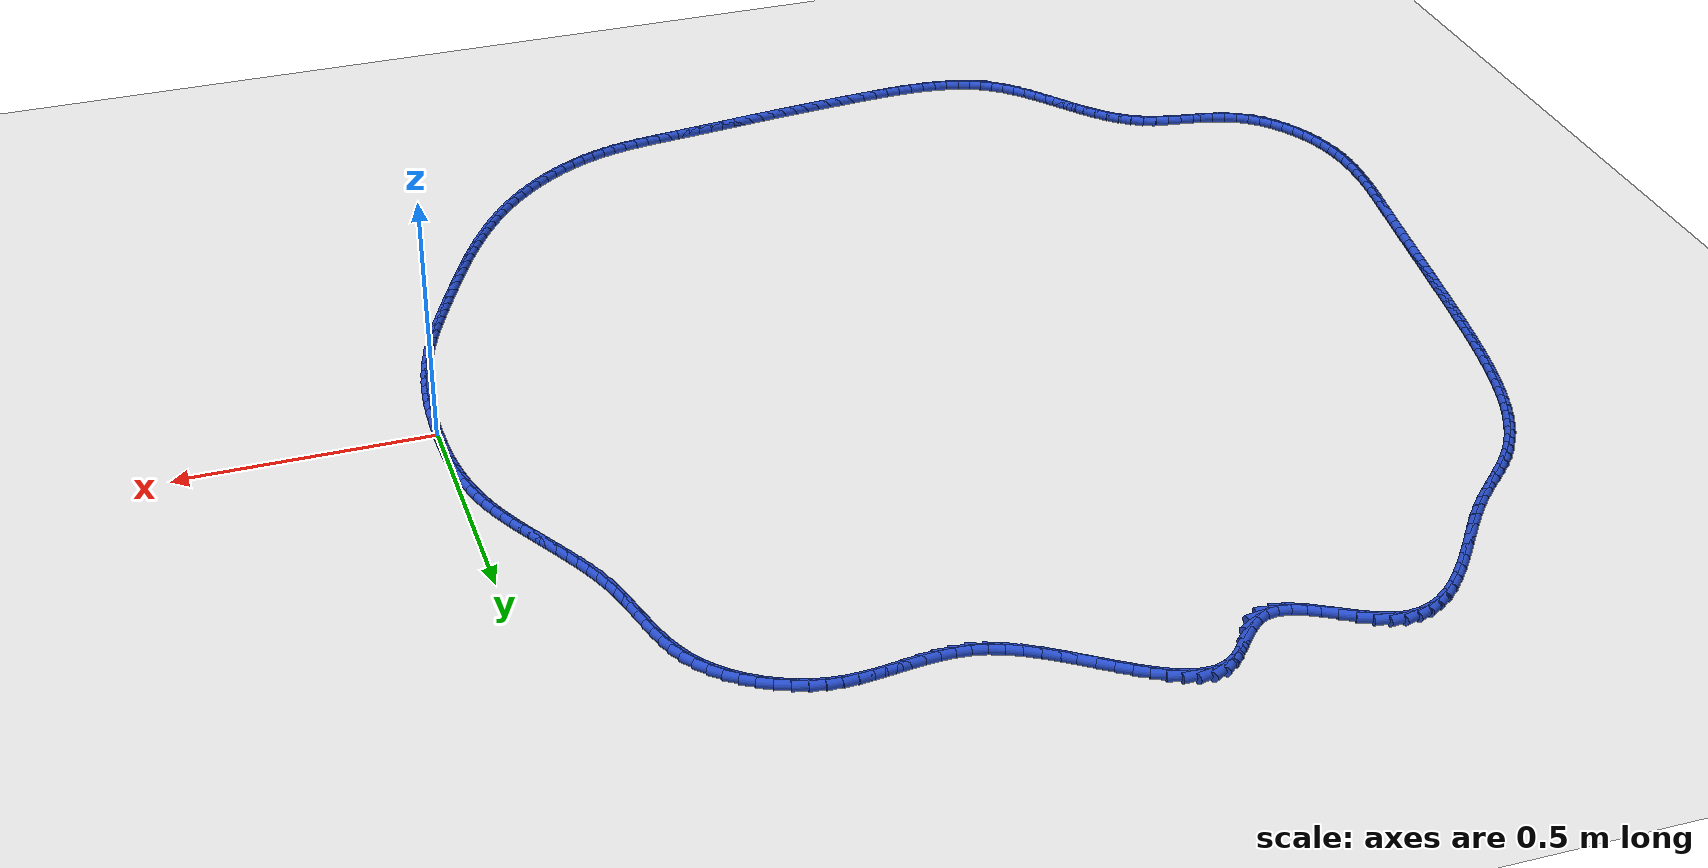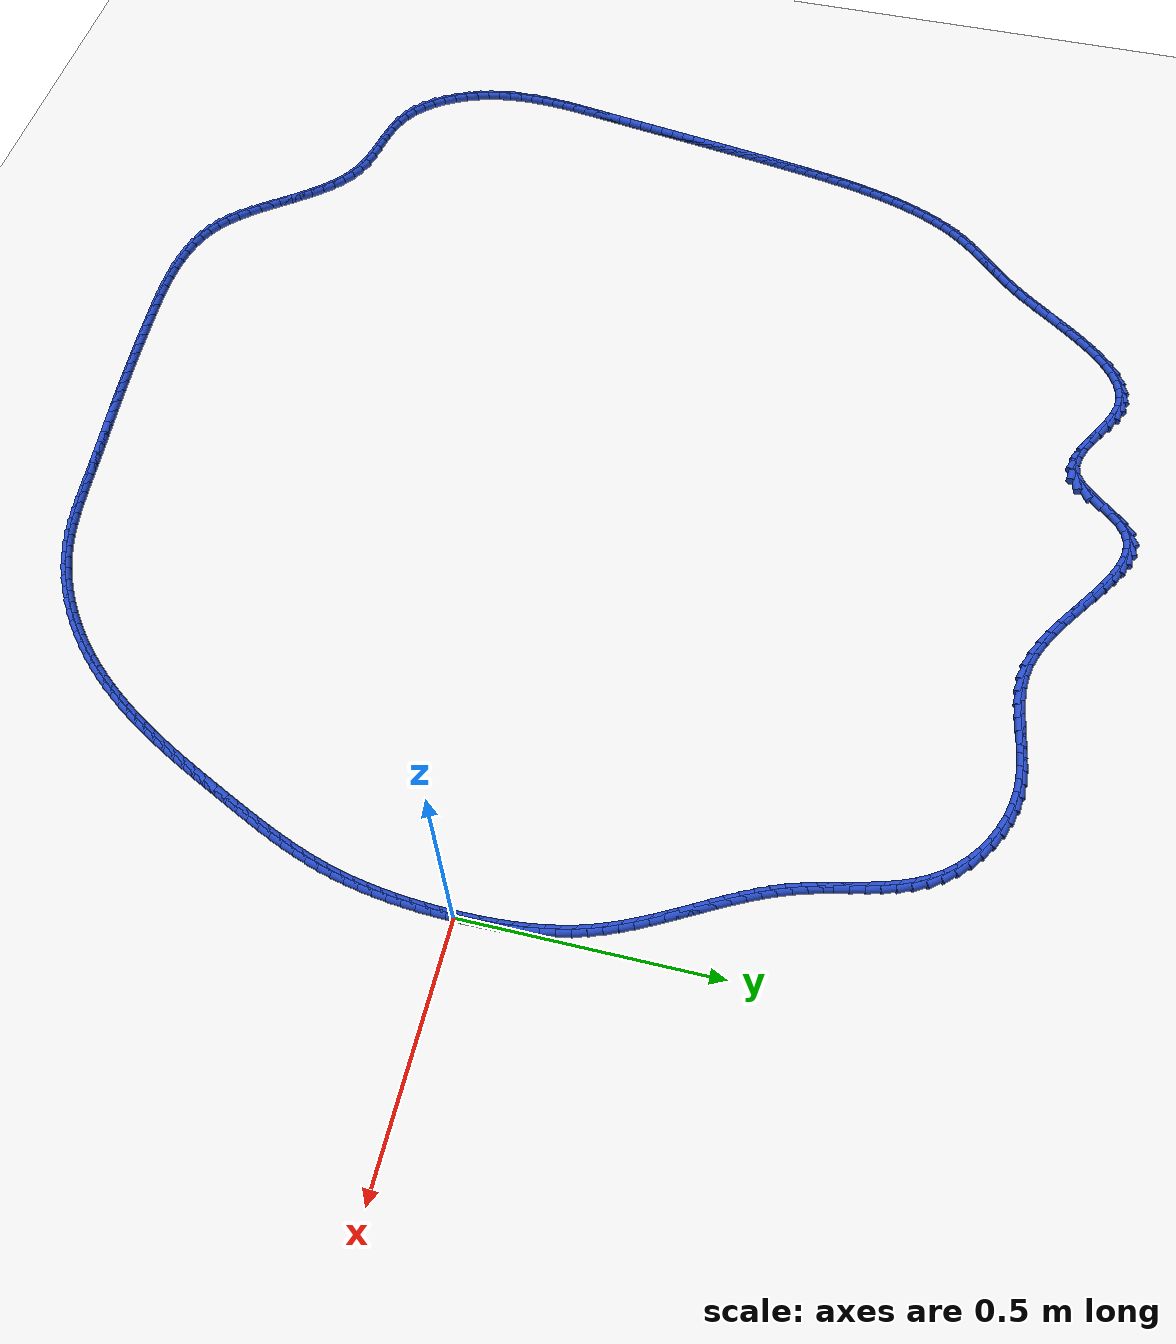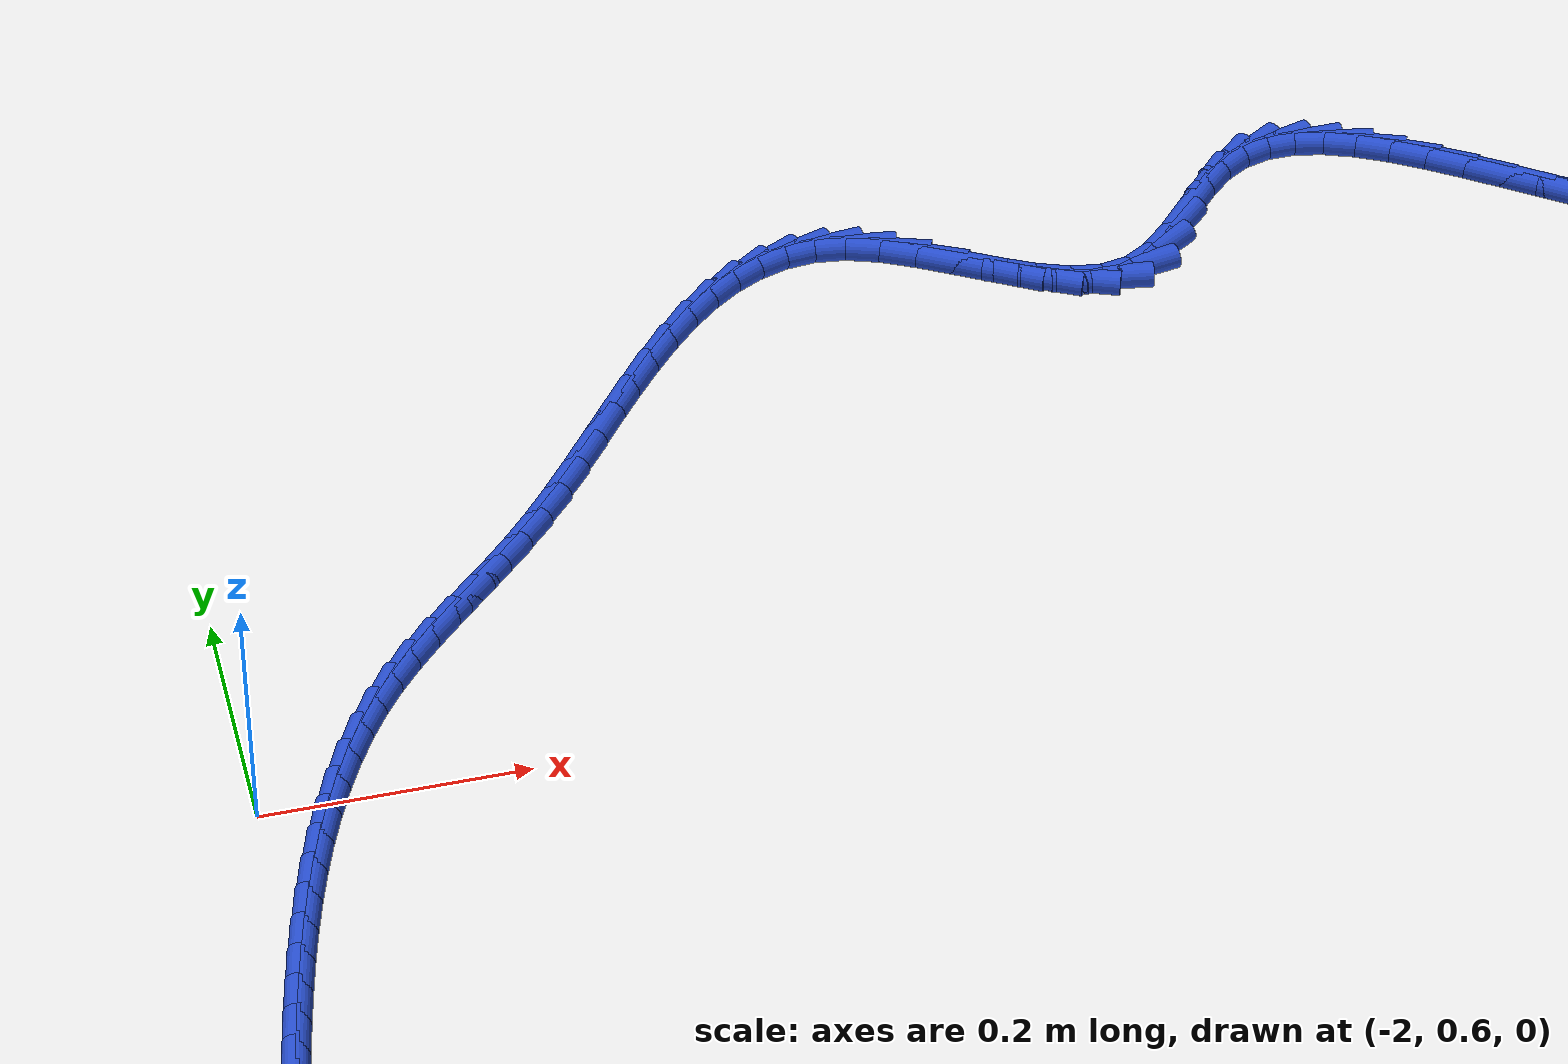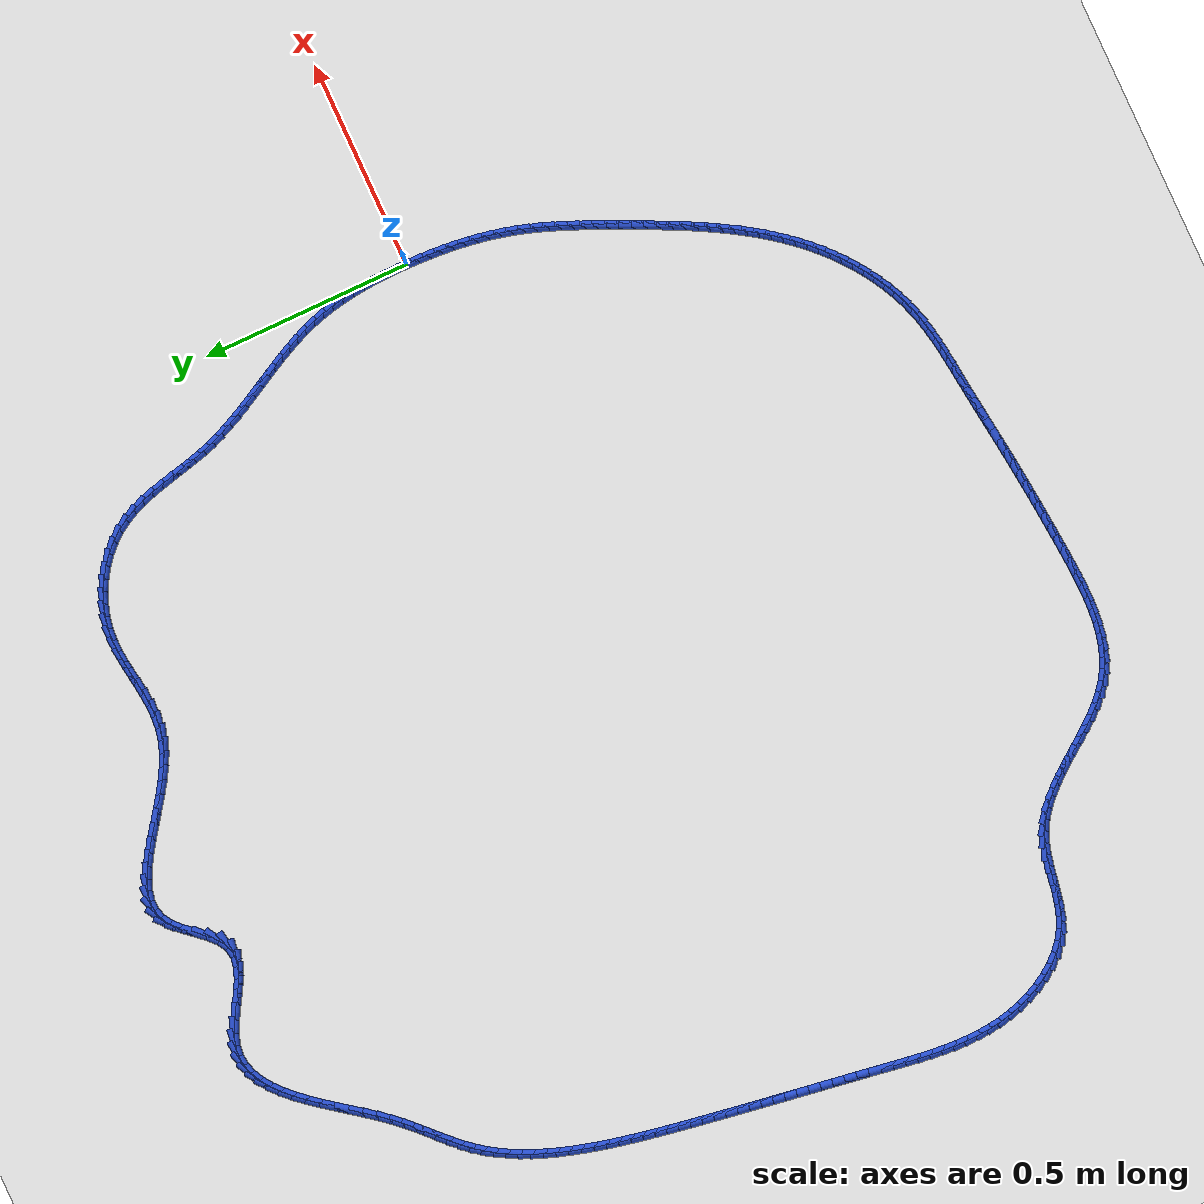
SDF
<sdf version="1.6">
 <world name="default">
  <light name="sun" type="directional">
   <pose>0 0 10 0 -0 0</pose>
   <diffuse>0.8 0.8 0.8 1</diffuse>
   <specular>0.2 0.2 0.2 1</specular>
   <attenuation>
    <range>1000</range>
    <constant>0.9</constant>
    <linear>0.01</linear>
    <quadratic>0.001</quadratic>
   </attenuation>
   <direction>-0.5 0.1 -0.9</direction>
  </light>
  <model name="ground_plane">
   <static>1</static>
   <link name="link">
    <collision name="collision">
     <geometry><plane><normal>0 0 1</normal><size>100 100</size></plane></geometry>
     <surface><friction><ode><mu>100</mu><mu2>50</mu2></ode></friction></surface>
    </collision>
    <visual name="visual">
     <cast_shadows>0</cast_shadows>
     <geometry><plane><normal>0 0 1</normal><size>100 100</size></plane></geometry>
     <material>
      <script><uri>file://media/materials/scripts/gazebo.material</uri><name>Gazebo/WhiteGlow</name></script>
     </material>
    </visual>
   </link>
  </model>
  <gravity>0 0 -9.8</gravity>
  <magnetic_field>6e-06 2.3e-05 -4.2e-05</magnetic_field>
  <atmosphere type="adiabatic"/>
  <physics name="default_physics" default="0" type="ode">
   <max_step_size>0.001</max_step_size>
   <real_time_factor>1</real_time_factor>
   <real_time_update_rate>1000</real_time_update_rate>
  </physics>
  <scene><ambient>0.4 0.4 0.4 1</ambient><background>0.7 0.7 0.7 1</background><shadows>1</shadows></scene>
  <spherical_coordinates>
   <surface_model>EARTH_WGS84</surface_model>
   <latitude_deg>0</latitude_deg>
   <longitude_deg>0</longitude_deg>
   <elevation>0</elevation>
   <heading_deg>0</heading_deg>
  </spherical_coordinates>
  <model name="line">
   <link name="link_0">
    <pose>1.3444106938820255e-17 -2.7755575615628914e-17 0.01 0 1.57 1.5701263349986416</pose>
    <collision name="collision">
     <geometry><cylinder><radius>0.01</radius><length>0.08</length></cylinder></geometry>
    </collision>
    <visual name="visual">
     <material>
      <script><name>Gazebo/Blue</name><uri>file://media/materials/scripts/gazebo.material</uri></script>
     </material>
     <geometry><cylinder><radius>0.01</radius><length>0.08</length></cylinder></geometry>
    </visual>
   </link>
   <link name="link_1">
    <pose>1.9040110375387982e-05 0.028418418901303238 0.01 0 1.57 -1.5478350162516283</pose>
    <collision name="collision">
     <geometry><cylinder><radius>0.01</radius><length>0.08</length></cylinder></geometry>
    </collision>
    <visual name="visual">
     <material>
      <script><name>Gazebo/Blue</name><uri>file://media/materials/scripts/gazebo.material</uri></script>
     </material>
     <geometry><cylinder><radius>0.01</radius><length>0.08</length></cylinder></geometry>
    </visual>
   </link>
   <link name="link_2">
    <pose>-0.0006334599822844407 0.05683079617593522 0.01 0 1.57 -1.520804407910332</pose>
    <collision name="collision">
     <geometry><cylinder><radius>0.01</radius><length>0.08</length></cylinder></geometry>
    </collision>
    <visual name="visual">
     <material>
      <script><name>Gazebo/Blue</name><uri>file://media/materials/scripts/gazebo.material</uri></script>
     </material>
     <geometry><cylinder><radius>0.01</radius><length>0.08</length></cylinder></geometry>
    </visual>
   </link>
   <link name="link_3">
    <pose>-0.0020515279072395305 0.08517310466058002 0.01 0 1.57 -1.490226430365436</pose>
    <collision name="collision">
     <geometry><cylinder><radius>0.01</radius><length>0.08</length></cylinder></geometry>
    </collision>
    <visual name="visual">
     <material>
      <script><name>Gazebo/Blue</name><uri>file://media/materials/scripts/gazebo.material</uri></script>
     </material>
     <geometry><cylinder><radius>0.01</radius><length>0.08</length></cylinder></geometry>
    </visual>
   </link>
   <link name="link_4">
    <pose>-0.004329191293749942 0.11338131719192161 0.01 0 1.57 -1.455942513833774</pose>
    <collision name="collision">
     <geometry><cylinder><radius>0.01</radius><length>0.08</length></cylinder></geometry>
    </collision>
    <visual name="visual">
     <material>
      <script><name>Gazebo/Blue</name><uri>file://media/materials/scripts/gazebo.material</uri></script>
     </material>
     <geometry><cylinder><radius>0.01</radius><length>0.08</length></cylinder></geometry>
    </visual>
   </link>
   <link name="link_5">
    <pose>-0.007560477771075736 0.14139140660664407 0.01 0 1.57 -1.4177941363192812</pose>
    <collision name="collision">
     <geometry><cylinder><radius>0.01</radius><length>0.08</length></cylinder></geometry>
    </collision>
    <visual name="visual">
     <material>
      <script><name>Gazebo/Blue</name><uri>file://media/materials/scripts/gazebo.material</uri></script>
     </material>
     <geometry><cylinder><radius>0.01</radius><length>0.08</length></cylinder></geometry>
    </visual>
   </link>
   <link name="link_6">
    <pose>-0.011839414968476968 0.16913934574143136 0.01 0 1.57 -1.3756366801889799</pose>
    <collision name="collision">
     <geometry><cylinder><radius>0.01</radius><length>0.08</length></cylinder></geometry>
    </collision>
    <visual name="visual">
     <material>
      <script><name>Gazebo/Blue</name><uri>file://media/materials/scripts/gazebo.material</uri></script>
     </material>
     <geometry><cylinder><radius>0.01</radius><length>0.08</length></cylinder></geometry>
    </visual>
   </link>
   <link name="link_7">
    <pose>-0.0172600305152137 0.19656110743296767 0.01 0 1.57 -1.3293571327558817</pose>
    <collision name="collision">
     <geometry><cylinder><radius>0.01</radius><length>0.08</length></cylinder></geometry>
    </collision>
    <visual name="visual">
     <material>
      <script><name>Gazebo/Blue</name><uri>file://media/materials/scripts/gazebo.material</uri></script>
     </material>
     <geometry><cylinder><radius>0.01</radius><length>0.08</length></cylinder></geometry>
    </visual>
   </link>
   <link name="link_8">
    <pose>-0.023916352040545992 0.22359266451793683 0.01 0 1.57 -1.278896113865314</pose>
    <collision name="collision">
     <geometry><cylinder><radius>0.01</radius><length>0.08</length></cylinder></geometry>
    </collision>
    <visual name="visual">
     <material>
      <script><name>Gazebo/Blue</name><uri>file://media/materials/scripts/gazebo.material</uri></script>
     </material>
     <geometry><cylinder><radius>0.01</radius><length>0.08</length></cylinder></geometry>
    </visual>
   </link>
   <link name="link_9">
    <pose>-0.03190239817348789 0.2501699942034586 0.01 0 1.57 -1.2266557137196805</pose>
    <collision name="collision">
     <geometry><cylinder><radius>0.01</radius><length>0.08</length></cylinder></geometry>
    </collision>
    <visual name="visual">
     <material>
      <script><name>Gazebo/Blue</name><uri>file://media/materials/scripts/gazebo.material</uri></script>
     </material>
     <geometry><cylinder><radius>0.01</radius><length>0.08</length></cylinder></geometry>
    </visual>
   </link>
   <link name="link_10">
    <pose>-0.04125243555958653 0.276258088702364 0.01 0 1.57 -1.1808705689488164</pose>
    <collision name="collision">
     <geometry><cylinder><radius>0.01</radius><length>0.08</length></cylinder></geometry>
    </collision>
    <visual name="visual">
     <material>
      <script><name>Gazebo/Blue</name><uri>file://media/materials/scripts/gazebo.material</uri></script>
     </material>
     <geometry><cylinder><radius>0.01</radius><length>0.08</length></cylinder></geometry>
    </visual>
   </link>
   <link name="link_11">
    <pose>-0.051798684649481605 0.30192005197472993 0.01 0 1.57 -1.1434134782884915</pose>
    <collision name="collision">
     <geometry><cylinder><radius>0.01</radius><length>0.08</length></cylinder></geometry>
    </collision>
    <visual name="visual">
     <material>
      <script><name>Gazebo/Blue</name><uri>file://media/materials/scripts/gazebo.material</uri></script>
     </material>
     <geometry><cylinder><radius>0.01</radius><length>0.08</length></cylinder></geometry>
    </visual>
   </link>
   <link name="link_12">
    <pose>-0.06333070257502467 0.3272397048902063 0.01 0 1.57 -1.114300253677261</pose>
    <collision name="collision">
     <geometry><cylinder><radius>0.01</radius><length>0.08</length></cylinder></geometry>
    </collision>
    <visual name="visual">
     <material>
      <script><name>Gazebo/Blue</name><uri>file://media/materials/scripts/gazebo.material</uri></script>
     </material>
     <geometry><cylinder><radius>0.01</radius><length>0.08</length></cylinder></geometry>
    </visual>
   </link>
   <link name="link_13">
    <pose>-0.07563804646806734 0.3523008683184433 0.01 0 1.57 -1.0934540482754938</pose>
    <collision name="collision">
     <geometry><cylinder><radius>0.01</radius><length>0.08</length></cylinder></geometry>
    </collision>
    <visual name="visual">
     <material>
      <script><name>Gazebo/Blue</name><uri>file://media/materials/scripts/gazebo.material</uri></script>
     </material>
     <geometry><cylinder><radius>0.01</radius><length>0.08</length></cylinder></geometry>
    </visual>
   </link>
   <link name="link_14">
    <pose>-0.08851027346046116 0.37718736312909085 0.01 0 1.57 -1.0807660921270414</pose>
    <collision name="collision">
     <geometry><cylinder><radius>0.01</radius><length>0.08</length></cylinder></geometry>
    </collision>
    <visual name="visual">
     <material>
      <script><name>Gazebo/Blue</name><uri>file://media/materials/scripts/gazebo.material</uri></script>
     </material>
     <geometry><cylinder><radius>0.01</radius><length>0.08</length></cylinder></geometry>
    </visual>
   </link>
   <link name="link_15">
    <pose>-0.10173694068405774 0.40198301019179916 0.01 0 1.57 -1.0761376303746737</pose>
    <collision name="collision">
     <geometry><cylinder><radius>0.01</radius><length>0.08</length></cylinder></geometry>
    </collision>
    <visual name="visual">
     <material>
      <script><name>Gazebo/Blue</name><uri>file://media/materials/scripts/gazebo.material</uri></script>
     </material>
     <geometry><cylinder><radius>0.01</radius><length>0.08</length></cylinder></geometry>
    </visual>
   </link>
   <link name="link_16">
    <pose>-0.11510760527070872 0.42677163037621824 0.01 0 1.57 -1.0795040976213326</pose>
    <collision name="collision">
     <geometry><cylinder><radius>0.01</radius><length>0.08</length></cylinder></geometry>
    </collision>
    <visual name="visual">
     <material>
      <script><name>Gazebo/Blue</name><uri>file://media/materials/scripts/gazebo.material</uri></script>
     </material>
     <geometry><cylinder><radius>0.01</radius><length>0.08</length></cylinder></geometry>
    </visual>
   </link>
   <link name="link_17">
    <pose>-0.1284118243522656 0.45163704455199816 0.01 0 1.57 -1.0908432139291977</pose>
    <collision name="collision">
     <geometry><cylinder><radius>0.01</radius><length>0.08</length></cylinder></geometry>
    </collision>
    <visual name="visual">
     <material>
      <script><name>Gazebo/Blue</name><uri>file://media/materials/scripts/gazebo.material</uri></script>
     </material>
     <geometry><cylinder><radius>0.01</radius><length>0.08</length></cylinder></geometry>
    </visual>
   </link>
   <link name="link_18">
    <pose>-0.14143915506058005 0.47666307358878907 0.01 0 1.57 -1.1101680971503363</pose>
    <collision name="collision">
     <geometry><cylinder><radius>0.01</radius><length>0.08</length></cylinder></geometry>
    </collision>
    <visual name="visual">
     <material>
      <script><name>Gazebo/Blue</name><uri>file://media/materials/scripts/gazebo.material</uri></script>
     </material>
     <geometry><cylinder><radius>0.01</radius><length>0.08</length></cylinder></geometry>
    </visual>
   </link>
   <link name="link_19">
    <pose>-0.15397915452750355 0.5019335383562409 0.01 0 1.57 -1.1375055177598266</pose>
    <collision name="collision">
     <geometry><cylinder><radius>0.01</radius><length>0.08</length></cylinder></geometry>
    </collision>
    <visual name="visual">
     <material>
      <script><name>Gazebo/Blue</name><uri>file://media/materials/scripts/gazebo.material</uri></script>
     </material>
     <geometry><cylinder><radius>0.01</radius><length>0.08</length></cylinder></geometry>
    </visual>
   </link>
   <link name="link_20">
    <pose>-0.16582137988488782 0.5275322597240039 0.01 0 1.57 -1.1728587956179286</pose>
    <collision name="collision">
     <geometry><cylinder><radius>0.01</radius><length>0.08</length></cylinder></geometry>
    </collision>
    <visual name="visual">
     <material>
      <script><name>Gazebo/Blue</name><uri>file://media/materials/scripts/gazebo.material</uri></script>
     </material>
     <geometry><cylinder><radius>0.01</radius><length>0.08</length></cylinder></geometry>
    </visual>
   </link>
   <link name="link_21">
    <pose>-0.17675538826458437 0.553543058561728 0.01 0 1.57 -1.216155259624458</pose>
    <collision name="collision">
     <geometry><cylinder><radius>0.01</radius><length>0.08</length></cylinder></geometry>
    </collision>
    <visual name="visual">
     <material>
      <script><name>Gazebo/Blue</name><uri>file://media/materials/scripts/gazebo.material</uri></script>
     </material>
     <geometry><cylinder><radius>0.01</radius><length>0.08</length></cylinder></geometry>
    </visual>
   </link>
   <link name="link_22">
    <pose>-0.18657073679844471 0.5800497557390633 0.01 0 1.57 -1.2657892929324055</pose>
    <collision name="collision">
     <geometry><cylinder><radius>0.01</radius><length>0.08</length></cylinder></geometry>
    </collision>
    <visual name="visual">
     <material>
      <script><name>Gazebo/Blue</name><uri>file://media/materials/scripts/gazebo.material</uri></script>
     </material>
     <geometry><cylinder><radius>0.01</radius><length>0.08</length></cylinder></geometry>
    </visual>
   </link>
   <link name="link_23">
    <pose>-0.1950931993404507 0.6071197192788982 0.01 0 1.57 -1.3067886795904688</pose>
    <collision name="collision">
     <geometry><cylinder><radius>0.01</radius><length>0.08</length></cylinder></geometry>
    </collision>
    <visual name="visual">
     <material>
      <script><name>Gazebo/Blue</name><uri>file://media/materials/scripts/gazebo.material</uri></script>
     </material>
     <geometry><cylinder><radius>0.01</radius><length>0.08</length></cylinder></geometry>
    </visual>
   </link>
   <link name="link_24">
    <pose>-0.20253383872016348 0.6346452847853522 0.01 0 1.57 -1.3305509640552622</pose>
    <collision name="collision">
     <geometry><cylinder><radius>0.01</radius><length>0.08</length></cylinder></geometry>
    </collision>
    <visual name="visual">
     <material>
      <script><name>Gazebo/Blue</name><uri>file://media/materials/scripts/gazebo.material</uri></script>
     </material>
     <geometry><cylinder><radius>0.01</radius><length>0.08</length></cylinder></geometry>
    </visual>
   </link>
   <link name="link_25">
    <pose>-0.2093363139412215 0.662413122054476 0.01 0 1.57 -1.3372827870785764</pose>
    <collision name="collision">
     <geometry><cylinder><radius>0.01</radius><length>0.08</length></cylinder></geometry>
    </collision>
    <visual name="visual">
     <material>
      <script><name>Gazebo/Blue</name><uri>file://media/materials/scripts/gazebo.material</uri></script>
     </material>
     <geometry><cylinder><radius>0.01</radius><length>0.08</length></cylinder></geometry>
    </visual>
   </link>
   <link name="link_26">
    <pose>-0.21594750210695585 0.6902084389360696 0.01 0 1.57 -1.327018796385844</pose>
    <collision name="collision">
     <geometry><cylinder><radius>0.01</radius><length>0.08</length></cylinder></geometry>
    </collision>
    <visual name="visual">
     <material>
      <script><name>Gazebo/Blue</name><uri>file://media/materials/scripts/gazebo.material</uri></script>
     </material>
     <geometry><cylinder><radius>0.01</radius><length>0.08</length></cylinder></geometry>
    </visual>
   </link>
   <link name="link_27">
    <pose>-0.22281428032069742 0.7178164432799337 0.01 0 1.57 -1.2994382978303265</pose>
    <collision name="collision">
     <geometry><cylinder><radius>0.01</radius><length>0.08</length></cylinder></geometry>
    </collision>
    <visual name="visual">
     <material>
      <script><name>Gazebo/Blue</name><uri>file://media/materials/scripts/gazebo.material</uri></script>
     </material>
     <geometry><cylinder><radius>0.01</radius><length>0.08</length></cylinder></geometry>
    </visual>
   </link>
   <link name="link_28">
    <pose>-0.23038352568577714 0.7450223429358682 0.01 0 1.57 -1.2539418290023816</pose>
    <collision name="collision">
     <geometry><cylinder><radius>0.01</radius><length>0.08</length></cylinder></geometry>
    </collision>
    <visual name="visual">
     <material>
      <script><name>Gazebo/Blue</name><uri>file://media/materials/scripts/gazebo.material</uri></script>
     </material>
     <geometry><cylinder><radius>0.01</radius><length>0.08</length></cylinder></geometry>
    </visual>
   </link>
   <link name="link_29">
    <pose>-0.23910211530552597 0.7716113457536737 0.01 0 1.57 -1.189892220184687</pose>
    <collision name="collision">
     <geometry><cylinder><radius>0.01</radius><length>0.08</length></cylinder></geometry>
    </collision>
    <visual name="visual">
     <material>
      <script><name>Gazebo/Blue</name><uri>file://media/materials/scripts/gazebo.material</uri></script>
     </material>
     <geometry><cylinder><radius>0.01</radius><length>0.08</length></cylinder></geometry>
    </visual>
   </link>
   <link name="link_30">
    <pose>-0.24941692628327483 0.7973686595831505 0.01 0 1.57 -1.1070680084785087</pose>
    <collision name="collision">
     <geometry><cylinder><radius>0.01</radius><length>0.08</length></cylinder></geometry>
    </collision>
    <visual name="visual">
     <material>
      <script><name>Gazebo/Blue</name><uri>file://media/materials/scripts/gazebo.material</uri></script>
     </material>
     <geometry><cylinder><radius>0.01</radius><length>0.08</length></cylinder></geometry>
    </visual>
   </link>
   <link name="link_31">
    <pose>-0.26177483572235477 0.8220794922740988 0.01 0 1.57 -1.0063335818160861</pose>
    <collision name="collision">
     <geometry><cylinder><radius>0.01</radius><length>0.08</length></cylinder></geometry>
    </collision>
    <visual name="visual">
     <material>
      <script><name>Gazebo/Blue</name><uri>file://media/materials/scripts/gazebo.material</uri></script>
     </material>
     <geometry><cylinder><radius>0.01</radius><length>0.08</length></cylinder></geometry>
    </visual>
   </link>
   <link name="link_32">
    <pose>-0.2766227195830525 0.845529051663795 0.01 0 1.57 -0.894278461633629</pose>
    <collision name="collision">
     <geometry><cylinder><radius>0.01</radius><length>0.08</length></cylinder></geometry>
    </collision>
    <visual name="visual">
     <material>
      <script><name>Gazebo/Blue</name><uri>file://media/materials/scripts/gazebo.material</uri></script>
     </material>
     <geometry><cylinder><radius>0.01</radius><length>0.08</length></cylinder></geometry>
    </visual>
   </link>
   <link name="link_33">
    <pose>-0.29426438142410216 0.867500977982338 0.01 0 1.57 -0.7871555242824446</pose>
    <collision name="collision">
     <geometry><cylinder><radius>0.01</radius><length>0.08</length></cylinder></geometry>
    </collision>
    <visual name="visual">
     <material>
      <script><name>Gazebo/Blue</name><uri>file://media/materials/scripts/gazebo.material</uri></script>
     </material>
     <geometry><cylinder><radius>0.01</radius><length>0.08</length></cylinder></geometry>
    </visual>
   </link>
   <link name="link_34">
    <pose>-0.314465290873548 0.8877730130746417 0.01 0 1.57 -0.6863180000720027</pose>
    <collision name="collision">
     <geometry><cylinder><radius>0.01</radius><length>0.08</length></cylinder></geometry>
    </collision>
    <visual name="visual">
     <material>
      <script><name>Gazebo/Blue</name><uri>file://media/materials/scripts/gazebo.material</uri></script>
     </material>
     <geometry><cylinder><radius>0.01</radius><length>0.08</length></cylinder></geometry>
    </visual>
   </link>
   <link name="link_35">
    <pose>-0.3368643249642868 0.9061215117434057 0.01 0 1.57 -0.5892572759337389</pose>
    <collision name="collision">
     <geometry><cylinder><radius>0.01</radius><length>0.08</length></cylinder></geometry>
    </collision>
    <visual name="visual">
     <material>
      <script><name>Gazebo/Blue</name><uri>file://media/materials/scripts/gazebo.material</uri></script>
     </material>
     <geometry><cylinder><radius>0.01</radius><length>0.08</length></cylinder></geometry>
    </visual>
   </link>
   <link name="link_36">
    <pose>-0.3611003607292149 0.9223228287913293 0.01 0 1.57 -0.4935074973112351</pose>
    <collision name="collision">
     <geometry><cylinder><radius>0.01</radius><length>0.08</length></cylinder></geometry>
    </collision>
    <visual name="visual">
     <material>
      <script><name>Gazebo/Blue</name><uri>file://media/materials/scripts/gazebo.material</uri></script>
     </material>
     <geometry><cylinder><radius>0.01</radius><length>0.08</length></cylinder></geometry>
    </visual>
   </link>
   <link name="link_37">
    <pose>-0.3868122752012287 0.9361533190211113 0.01 0 1.57 -0.3966394838077963</pose>
    <collision name="collision">
     <geometry><cylinder><radius>0.01</radius><length>0.08</length></cylinder></geometry>
    </collision>
    <visual name="visual">
     <material>
      <script><name>Gazebo/Blue</name><uri>file://media/materials/scripts/gazebo.material</uri></script>
     </material>
     <geometry><cylinder><radius>0.01</radius><length>0.08</length></cylinder></geometry>
    </visual>
   </link>
   <link name="link_38">
    <pose>-0.41363894541322527 0.9473893372354516 0.01 0 1.57 -0.2962336021896722</pose>
    <collision name="collision">
     <geometry><cylinder><radius>0.01</radius><length>0.08</length></cylinder></geometry>
    </collision>
    <visual name="visual">
     <material>
      <script><name>Gazebo/Blue</name><uri>file://media/materials/scripts/gazebo.material</uri></script>
     </material>
     <geometry><cylinder><radius>0.01</radius><length>0.08</length></cylinder></geometry>
    </visual>
   </link>
   <link name="link_39">
    <pose>-0.44121924839810067 0.9558072382370489 0.01 0 1.57 -0.18987629706242729</pose>
    <collision name="collision">
     <geometry><cylinder><radius>0.01</radius><length>0.08</length></cylinder></geometry>
    </collision>
    <visual name="visual">
     <material>
      <script><name>Gazebo/Blue</name><uri>file://media/materials/scripts/gazebo.material</uri></script>
     </material>
     <geometry><cylinder><radius>0.01</radius><length>0.08</length></cylinder></geometry>
    </visual>
   </link>
   <link name="link_40">
    <pose>-0.46919206118875145 0.9611833768286024 0.01 0 1.57 -0.07848373821105482</pose>
    <collision name="collision">
     <geometry><cylinder><radius>0.01</radius><length>0.08</length></cylinder></geometry>
    </collision>
    <visual name="visual">
     <material>
      <script><name>Gazebo/Blue</name><uri>file://media/materials/scripts/gazebo.material</uri></script>
     </material>
     <geometry><cylinder><radius>0.01</radius><length>0.08</length></cylinder></geometry>
    </visual>
   </link>
   <link name="link_41">
    <pose>-0.49723121199268305 0.9633885237393826 0.01 0 1.57 0.01634159145770869</pose>
    <collision name="collision">
     <geometry><cylinder><radius>0.01</radius><length>0.08</length></cylinder></geometry>
    </collision>
    <visual name="visual">
     <material>
      <script><name>Gazebo/Blue</name><uri>file://media/materials/scripts/gazebo.material</uri></script>
     </material>
     <geometry><cylinder><radius>0.01</radius><length>0.08</length></cylinder></geometry>
    </visual>
   </link>
   <link name="link_42">
    <pose>-0.5252464171446485 0.9629306699452056 0.01 0 1.57 0.08371373332486362</pose>
    <collision name="collision">
     <geometry><cylinder><radius>0.01</radius><length>0.08</length></cylinder></geometry>
    </collision>
    <visual name="visual">
     <material>
      <script><name>Gazebo/Blue</name><uri>file://media/materials/scripts/gazebo.material</uri></script>
     </material>
     <geometry><cylinder><radius>0.01</radius><length>0.08</length></cylinder></geometry>
    </visual>
   </link>
   <link name="link_43">
    <pose>-0.5532449406345098 0.9605813183737756 0.01 0 1.57 0.12329362729203241</pose>
    <collision name="collision">
     <geometry><cylinder><radius>0.01</radius><length>0.08</length></cylinder></geometry>
    </collision>
    <visual name="visual">
     <material>
      <script><name>Gazebo/Blue</name><uri>file://media/materials/scripts/gazebo.material</uri></script>
     </material>
     <geometry><cylinder><radius>0.01</radius><length>0.08</length></cylinder></geometry>
    </visual>
   </link>
   <link name="link_44">
    <pose>-0.5812343561871295 0.9571128086605015 0.01 0 1.57 0.13548558379407333</pose>
    <collision name="collision">
     <geometry><cylinder><radius>0.01</radius><length>0.08</length></cylinder></geometry>
    </collision>
    <visual name="visual">
     <material>
      <script><name>Gazebo/Blue</name><uri>file://media/materials/scripts/gazebo.material</uri></script>
     </material>
     <geometry><cylinder><radius>0.01</radius><length>0.08</length></cylinder></geometry>
    </visual>
   </link>
   <link name="link_45">
    <pose>-0.6092222375273703 0.9532974804407918 0.01 0 1.57 0.12050413117563119</pose>
    <collision name="collision">
     <geometry><cylinder><radius>0.01</radius><length>0.08</length></cylinder></geometry>
    </collision>
    <visual name="visual">
     <material>
      <script><name>Gazebo/Blue</name><uri>file://media/materials/scripts/gazebo.material</uri></script>
     </material>
     <geometry><cylinder><radius>0.01</radius><length>0.08</length></cylinder></geometry>
    </visual>
   </link>
   <link name="link_46">
    <pose>-0.6372161583800946 0.9499076733500558 0.01 0 1.57 0.07810353562635447</pose>
    <collision name="collision">
     <geometry><cylinder><radius>0.01</radius><length>0.08</length></cylinder></geometry>
    </collision>
    <visual name="visual">
     <material>
      <script><name>Gazebo/Blue</name><uri>file://media/materials/scripts/gazebo.material</uri></script>
     </material>
     <geometry><cylinder><radius>0.01</radius><length>0.08</length></cylinder></geometry>
    </visual>
   </link>
   <link name="link_47">
    <pose>-0.6652236924701649 0.9477157270237014 0.01 0 1.57 0.007911217210608718</pose>
    <collision name="collision">
     <geometry><cylinder><radius>0.01</radius><length>0.08</length></cylinder></geometry>
    </collision>
    <visual name="visual">
     <material>
      <script><name>Gazebo/Blue</name><uri>file://media/materials/scripts/gazebo.material</uri></script>
     </material>
     <geometry><cylinder><radius>0.01</radius><length>0.08</length></cylinder></geometry>
    </visual>
   </link>
   <link name="link_48">
    <pose>-0.6932524135224438 0.9474939810971381 0.01 0 1.57 -0.08960334484534141</pose>
    <collision name="collision">
     <geometry><cylinder><radius>0.01</radius><length>0.08</length></cylinder></geometry>
    </collision>
    <visual name="visual">
     <material>
      <script><name>Gazebo/Blue</name><uri>file://media/materials/scripts/gazebo.material</uri></script>
     </material>
     <geometry><cylinder><radius>0.01</radius><length>0.08</length></cylinder></geometry>
    </visual>
   </link>
   <link name="link_49">
    <pose>-0.7213098952617942 0.9500147752057746 0.01 0 1.57 -0.21162316478883456</pose>
    <collision name="collision">
     <geometry><cylinder><radius>0.01</radius><length>0.08</length></cylinder></geometry>
    </collision>
    <visual name="visual">
     <material>
      <script><name>Gazebo/Blue</name><uri>file://media/materials/scripts/gazebo.material</uri></script>
     </material>
     <geometry><cylinder><radius>0.01</radius><length>0.08</length></cylinder></geometry>
    </visual>
   </link>
   <link name="link_50">
    <pose>-0.7494037114097462 0.9560504489203547 0.01 0 1.57 -0.34343479795915616</pose>
    <collision name="collision">
     <geometry><cylinder><radius>0.01</radius><length>0.08</length></cylinder></geometry>
    </collision>
    <visual name="visual">
     <material>
      <script><name>Gazebo/Blue</name><uri>file://media/materials/scripts/gazebo.material</uri></script>
     </material>
     <geometry><cylinder><radius>0.01</radius><length>0.08</length></cylinder></geometry>
    </visual>
   </link>
   <link name="link_51">
    <pose>-0.7775277509767594 0.9661077795008626 0.01 0 1.57 -0.44919716350614924</pose>
    <collision name="collision">
     <geometry><cylinder><radius>0.01</radius><length>0.08</length></cylinder></geometry>
    </collision>
    <visual name="visual">
     <material>
      <script><name>Gazebo/Blue</name><uri>file://media/materials/scripts/gazebo.material</uri></script>
     </material>
     <geometry><cylinder><radius>0.01</radius><length>0.08</length></cylinder></geometry>
    </visual>
   </link>
   <link name="link_52">
    <pose>-0.8056221863145253 0.9796511312578662 0.01 0 1.57 -0.5256570968957178</pose>
    <collision name="collision">
     <geometry><cylinder><radius>0.01</radius><length>0.08</length></cylinder></geometry>
    </collision>
    <visual name="visual">
     <material>
      <script><name>Gazebo/Blue</name><uri>file://media/materials/scripts/gazebo.material</uri></script>
     </material>
     <geometry><cylinder><radius>0.01</radius><length>0.08</length></cylinder></geometry>
    </visual>
   </link>
   <link name="link_53">
    <pose>-0.8336140114021082 0.9958891320769175 0.01 0 1.57 -0.577908797847344</pose>
    <collision name="collision">
     <geometry><cylinder><radius>0.01</radius><length>0.08</length></cylinder></geometry>
    </collision>
    <visual name="visual">
     <material>
      <script><name>Gazebo/Blue</name><uri>file://media/materials/scripts/gazebo.material</uri></script>
     </material>
     <geometry><cylinder><radius>0.01</radius><length>0.08</length></cylinder></geometry>
    </visual>
   </link>
   <link name="link_54">
    <pose>-0.8614302202185751 1.0140304098435708 0.01 0 1.57 -0.6096508480563497</pose>
    <collision name="collision">
     <geometry><cylinder><radius>0.01</radius><length>0.08</length></cylinder></geometry>
    </collision>
    <visual name="visual">
     <material>
      <script><name>Gazebo/Blue</name><uri>file://media/materials/scripts/gazebo.material</uri></script>
     </material>
     <geometry><cylinder><radius>0.01</radius><length>0.08</length></cylinder></geometry>
    </visual>
   </link>
   <link name="link_55">
    <pose>-0.8889978067429898 1.0332835924433783 0.01 0 1.57 -0.6229738127213336</pose>
    <collision name="collision">
     <geometry><cylinder><radius>0.01</radius><length>0.08</length></cylinder></geometry>
    </collision>
    <visual name="visual">
     <material>
      <script><name>Gazebo/Blue</name><uri>file://media/materials/scripts/gazebo.material</uri></script>
     </material>
     <geometry><cylinder><radius>0.01</radius><length>0.08</length></cylinder></geometry>
    </visual>
   </link>
   <link name="link_56">
    <pose>-0.9162437649544183 1.0528573077618932 0.01 0 1.57 -0.6183569386729377</pose>
    <collision name="collision">
     <geometry><cylinder><radius>0.01</radius><length>0.08</length></cylinder></geometry>
    </collision>
    <visual name="visual">
     <material>
      <script><name>Gazebo/Blue</name><uri>file://media/materials/scripts/gazebo.material</uri></script>
     </material>
     <geometry><cylinder><radius>0.01</radius><length>0.08</length></cylinder></geometry>
    </visual>
   </link>
   <link name="link_57">
    <pose>-0.943095088831926 1.0719601836846686 0.01 0 1.57 -0.5945740543337875</pose>
    <collision name="collision">
     <geometry><cylinder><radius>0.01</radius><length>0.08</length></cylinder></geometry>
    </collision>
    <visual name="visual">
     <material>
      <script><name>Gazebo/Blue</name><uri>file://media/materials/scripts/gazebo.material</uri></script>
     </material>
     <geometry><cylinder><radius>0.01</radius><length>0.08</length></cylinder></geometry>
    </visual>
   </link>
   <link name="link_58">
    <pose>-0.9694787723545778 1.089800848097257 0.01 0 1.57 -0.5483835461081852</pose>
    <collision name="collision">
     <geometry><cylinder><radius>0.01</radius><length>0.08</length></cylinder></geometry>
    </collision>
    <visual name="visual">
     <material>
      <script><name>Gazebo/Blue</name><uri>file://media/materials/scripts/gazebo.material</uri></script>
     </material>
     <geometry><cylinder><radius>0.01</radius><length>0.08</length></cylinder></geometry>
    </visual>
   </link>
   <link name="link_59">
    <pose>-0.9953218095014391 1.1055879288852113 0.01 0 1.57 -0.4739762023925113</pose>
    <collision name="collision">
     <geometry><cylinder><radius>0.01</radius><length>0.08</length></cylinder></geometry>
    </collision>
    <visual name="visual">
     <material>
      <script><name>Gazebo/Blue</name><uri>file://media/materials/scripts/gazebo.material</uri></script>
     </material>
     <geometry><cylinder><radius>0.01</radius><length>0.08</length></cylinder></geometry>
    </visual>
   </link>
   <link name="link_60">
    <pose>-1.0205511942515753 1.118530053934085 0.01 0 1.57 -0.3624191044341295</pose>
    <collision name="collision">
     <geometry><cylinder><radius>0.01</radius><length>0.08</length></cylinder></geometry>
    </collision>
    <visual name="visual">
     <material>
      <script><name>Gazebo/Blue</name><uri>file://media/materials/scripts/gazebo.material</uri></script>
     </material>
     <geometry><cylinder><radius>0.01</radius><length>0.08</length></cylinder></geometry>
    </visual>
   </link>
   <link name="link_61">
    <pose>-1.0450939205840517 1.1278358511294306 0.01 0 1.57 -0.2023022781026082</pose>
    <collision name="collision">
     <geometry><cylinder><radius>0.01</radius><length>0.08</length></cylinder></geometry>
    </collision>
    <visual name="visual">
     <material>
      <script><name>Gazebo/Blue</name><uri>file://media/materials/scripts/gazebo.material</uri></script>
     </material>
     <geometry><cylinder><radius>0.01</radius><length>0.08</length></cylinder></geometry>
    </visual>
   </link>
   <link name="link_62">
    <pose>-1.0688769824779338 1.1327139483568016 0.01 0 1.57 0.014855945763422194</pose>
    <collision name="collision">
     <geometry><cylinder><radius>0.01</radius><length>0.08</length></cylinder></geometry>
    </collision>
    <visual name="visual">
     <material>
      <script><name>Gazebo/Blue</name><uri>file://media/materials/scripts/gazebo.material</uri></script>
     </material>
     <geometry><cylinder><radius>0.01</radius><length>0.08</length></cylinder></geometry>
    </visual>
   </link>
   <link name="link_63">
    <pose>-1.0918273739122868 1.1323729735017505 0.01 0 1.57 0.28051802848266894</pose>
    <collision name="collision">
     <geometry><cylinder><radius>0.01</radius><length>0.08</length></cylinder></geometry>
    </collision>
    <visual name="visual">
     <material>
      <script><name>Gazebo/Blue</name><uri>file://media/materials/scripts/gazebo.material</uri></script>
     </material>
     <geometry><cylinder><radius>0.01</radius><length>0.08</length></cylinder></geometry>
    </visual>
   </link>
   <link name="link_64">
    <pose>-1.113872088866176 1.1260215544498302 0.01 0 1.57 0.5576078184713305</pose>
    <collision name="collision">
     <geometry><cylinder><radius>0.01</radius><length>0.08</length></cylinder></geometry>
    </collision>
    <visual name="visual">
     <material>
      <script><name>Gazebo/Blue</name><uri>file://media/materials/scripts/gazebo.material</uri></script>
     </material>
     <geometry><cylinder><radius>0.01</radius><length>0.08</length></cylinder></geometry>
    </visual>
   </link>
   <link name="link_65">
    <pose>-1.1349402924138037 1.1128829580982396 0.01 0 1.57 0.7637106657214349</pose>
    <collision name="collision">
     <geometry><cylinder><radius>0.01</radius><length>0.08</length></cylinder></geometry>
    </collision>
    <visual name="visual">
     <material>
      <script><name>Gazebo/Blue</name><uri>file://media/materials/scripts/gazebo.material</uri></script>
     </material>
     <geometry><cylinder><radius>0.01</radius><length>0.08</length></cylinder></geometry>
    </visual>
   </link>
   <link name="link_66">
    <pose>-1.1551600725055178 1.0935217257317231 0.01 0 1.57 0.8503595775195396</pose>
    <collision name="collision">
     <geometry><cylinder><radius>0.01</radius><length>0.08</length></cylinder></geometry>
    </collision>
    <visual name="visual">
     <material>
      <script><name>Gazebo/Blue</name><uri>file://media/materials/scripts/gazebo.material</uri></script>
     </material>
     <geometry><cylinder><radius>0.01</radius><length>0.08</length></cylinder></geometry>
    </visual>
   </link>
   <link name="link_67">
    <pose>-1.175015571800816 1.0709031635505701 0.01 0 1.57 0.8473927391355018</pose>
    <collision name="collision">
     <geometry><cylinder><radius>0.01</radius><length>0.08</length></cylinder></geometry>
    </collision>
    <visual name="visual">
     <material>
      <script><name>Gazebo/Blue</name><uri>file://media/materials/scripts/gazebo.material</uri></script>
     </material>
     <geometry><cylinder><radius>0.01</radius><length>0.08</length></cylinder></geometry>
    </visual>
   </link>
   <link name="link_68">
    <pose>-1.1950279095822862 1.0482418994944798 0.01 0 1.57 0.755517350616917</pose>
    <collision name="collision">
     <geometry><cylinder><radius>0.01</radius><length>0.08</length></cylinder></geometry>
    </collision>
    <visual name="visual">
     <material>
      <script><name>Gazebo/Blue</name><uri>file://media/materials/scripts/gazebo.material</uri></script>
     </material>
     <geometry><cylinder><radius>0.01</radius><length>0.08</length></cylinder></geometry>
    </visual>
   </link>
   <link name="link_69">
    <pose>-1.2157182051325164 1.0287525615031514 0.01 0 1.57 0.5393829126443814</pose>
    <collision name="collision">
     <geometry><cylinder><radius>0.01</radius><length>0.08</length></cylinder></geometry>
    </collision>
    <visual name="visual">
     <material>
      <script><name>Gazebo/Blue</name><uri>file://media/materials/scripts/gazebo.material</uri></script>
     </material>
     <geometry><cylinder><radius>0.01</radius><length>0.08</length></cylinder></geometry>
    </visual>
   </link>
   <link name="link_70">
    <pose>-1.237607577734095 1.015649777516284 0.01 0 1.57 0.17322972556471875</pose>
    <collision name="collision">
     <geometry><cylinder><radius>0.01</radius><length>0.08</length></cylinder></geometry>
    </collision>
    <visual name="visual">
     <material>
      <script><name>Gazebo/Blue</name><uri>file://media/materials/scripts/gazebo.material</uri></script>
     </material>
     <geometry><cylinder><radius>0.01</radius><length>0.08</length></cylinder></geometry>
    </visual>
   </link>
   <link name="link_71">
    <pose>-1.2611154528167328 1.0115362855884427 0.01 0 1.57 -0.15930060286154848</pose>
    <collision name="collision">
     <geometry><cylinder><radius>0.01</radius><length>0.08</length></cylinder></geometry>
    </collision>
    <visual name="visual">
     <material>
      <script><name>Gazebo/Blue</name><uri>file://media/materials/scripts/gazebo.material</uri></script>
     </material>
     <geometry><cylinder><radius>0.01</radius><length>0.08</length></cylinder></geometry>
    </visual>
   </link>
   <link name="link_72">
    <pose>-1.2860850746495927 1.015547953219374 0.01 0 1.57 -0.3680241917864164</pose>
    <collision name="collision">
     <geometry><cylinder><radius>0.01</radius><length>0.08</length></cylinder></geometry>
    </collision>
    <visual name="visual">
     <material>
      <script><name>Gazebo/Blue</name><uri>file://media/materials/scripts/gazebo.material</uri></script>
     </material>
     <geometry><cylinder><radius>0.01</radius><length>0.08</length></cylinder></geometry>
    </visual>
   </link>
   <link name="link_73">
    <pose>-1.312156998938351 1.0256010748636348 0.01 0 1.57 -0.4814533472742842</pose>
    <collision name="collision">
     <geometry><cylinder><radius>0.01</radius><length>0.08</length></cylinder></geometry>
    </collision>
    <visual name="visual">
     <material>
      <script><name>Gazebo/Blue</name><uri>file://media/materials/scripts/gazebo.material</uri></script>
     </material>
     <geometry><cylinder><radius>0.01</radius><length>0.08</length></cylinder></geometry>
    </visual>
   </link>
   <link name="link_74">
    <pose>-1.3389715571163774 1.0396105955337815 0.01 0 1.57 -0.5285034687657213</pose>
    <collision name="collision">
     <geometry><cylinder><radius>0.01</radius><length>0.08</length></cylinder></geometry>
    </collision>
    <visual name="visual">
     <material>
      <script><name>Gazebo/Blue</name><uri>file://media/materials/scripts/gazebo.material</uri></script>
     </material>
     <geometry><cylinder><radius>0.01</radius><length>0.08</length></cylinder></geometry>
    </visual>
   </link>
   <link name="link_75">
    <pose>-1.3661690806170408 1.0554914602423708 0.01 0 1.57 -0.5222533344221536</pose>
    <collision name="collision">
     <geometry><cylinder><radius>0.01</radius><length>0.08</length></cylinder></geometry>
    </collision>
    <visual name="visual">
     <material>
      <script><name>Gazebo/Blue</name><uri>file://media/materials/scripts/gazebo.material</uri></script>
     </material>
     <geometry><cylinder><radius>0.01</radius><length>0.08</length></cylinder></geometry>
    </visual>
   </link>
   <link name="link_76">
    <pose>-1.3933899008737094 1.0711586140019587 0.01 0 1.57 -0.46144804787417953</pose>
    <collision name="collision">
     <geometry><cylinder><radius>0.01</radius><length>0.08</length></cylinder></geometry>
    </collision>
    <visual name="visual">
     <material>
      <script><name>Gazebo/Blue</name><uri>file://media/materials/scripts/gazebo.material</uri></script>
     </material>
     <geometry><cylinder><radius>0.01</radius><length>0.08</length></cylinder></geometry>
    </visual>
   </link>
   <link name="link_77">
    <pose>-1.4202743493197523 1.0845270018251014 0.01 0 1.57 -0.33052075730867514</pose>
    <collision name="collision">
     <geometry><cylinder><radius>0.01</radius><length>0.08</length></cylinder></geometry>
    </collision>
    <visual name="visual">
     <material>
      <script><name>Gazebo/Blue</name><uri>file://media/materials/scripts/gazebo.material</uri></script>
     </material>
     <geometry><cylinder><radius>0.01</radius><length>0.08</length></cylinder></geometry>
    </visual>
   </link>
   <link name="link_78">
    <pose>-1.4464629099650776 1.0935124757365826 0.01 0 1.57 -0.12413352134393098</pose>
    <collision name="collision">
     <geometry><cylinder><radius>0.01</radius><length>0.08</length></cylinder></geometry>
    </collision>
    <visual name="visual">
     <material>
      <script><name>Gazebo/Blue</name><uri>file://media/materials/scripts/gazebo.material</uri></script>
     </material>
     <geometry><cylinder><radius>0.01</radius><length>0.08</length></cylinder></geometry>
    </visual>
   </link>
   <link name="link_79">
    <pose>-1.4717021826323473 1.0966617078135295 0.01 0 1.57 0.09863293272439963</pose>
    <collision name="collision">
     <geometry><cylinder><radius>0.01</radius><length>0.08</length></cylinder></geometry>
    </collision>
    <visual name="visual">
     <material>
      <script><name>Gazebo/Blue</name><uri>file://media/materials/scripts/gazebo.material</uri></script>
     </material>
     <geometry><cylinder><radius>0.01</radius><length>0.08</length></cylinder></geometry>
    </visual>
   </link>
   <link name="link_80">
    <pose>-1.496030285971788 1.0942543439216377 0.01 0 1.57 0.3045942322500064</pose>
    <collision name="collision">
     <geometry><cylinder><radius>0.01</radius><length>0.08</length></cylinder></geometry>
    </collision>
    <visual name="visual">
     <material>
      <script><name>Gazebo/Blue</name><uri>file://media/materials/scripts/gazebo.material</uri></script>
     </material>
     <geometry><cylinder><radius>0.01</radius><length>0.08</length></cylinder></geometry>
    </visual>
   </link>
   <link name="link_81">
    <pose>-1.5195349595253058 1.0868650081459335 0.01 0 1.57 0.4780250759023559</pose>
    <collision name="collision">
     <geometry><cylinder><radius>0.01</radius><length>0.08</length></cylinder></geometry>
    </collision>
    <visual name="visual">
     <material>
      <script><name>Gazebo/Blue</name><uri>file://media/materials/scripts/gazebo.material</uri></script>
     </material>
     <geometry><cylinder><radius>0.01</radius><length>0.08</length></cylinder></geometry>
    </visual>
   </link>
   <link name="link_82">
    <pose>-1.542303942834812 1.0750683245714436 0.01 0 1.57 0.6151021428546527</pose>
    <collision name="collision">
     <geometry><cylinder><radius>0.01</radius><length>0.08</length></cylinder></geometry>
    </collision>
    <visual name="visual">
     <material>
      <script><name>Gazebo/Blue</name><uri>file://media/materials/scripts/gazebo.material</uri></script>
     </material>
     <geometry><cylinder><radius>0.01</radius><length>0.08</length></cylinder></geometry>
    </visual>
   </link>
   <link name="link_83">
    <pose>-1.564424975442214 1.059438917283195 0.01 0 1.57 0.7194020563652869</pose>
    <collision name="collision">
     <geometry><cylinder><radius>0.01</radius><length>0.08</length></cylinder></geometry>
    </collision>
    <visual name="visual">
     <material>
      <script><name>Gazebo/Blue</name><uri>file://media/materials/scripts/gazebo.material</uri></script>
     </material>
     <geometry><cylinder><radius>0.01</radius><length>0.08</length></cylinder></geometry>
    </visual>
   </link>
   <link name="link_84">
    <pose>-1.5859857968894213 1.0405514103662141 0.01 0 1.57 0.796711327840984</pose>
    <collision name="collision">
     <geometry><cylinder><radius>0.01</radius><length>0.08</length></cylinder></geometry>
    </collision>
    <visual name="visual">
     <material>
      <script><name>Gazebo/Blue</name><uri>file://media/materials/scripts/gazebo.material</uri></script>
     </material>
     <geometry><cylinder><radius>0.01</radius><length>0.08</length></cylinder></geometry>
    </visual>
   </link>
   <link name="link_85">
    <pose>-1.6070741467183427 1.0189804279055281 0.01 0 1.57 0.8523548122086584</pose>
    <collision name="collision">
     <geometry><cylinder><radius>0.01</radius><length>0.08</length></cylinder></geometry>
    </collision>
    <visual name="visual">
     <material>
      <script><name>Gazebo/Blue</name><uri>file://media/materials/scripts/gazebo.material</uri></script>
     </material>
     <geometry><cylinder><radius>0.01</radius><length>0.08</length></cylinder></geometry>
    </visual>
   </link>
   <link name="link_86">
    <pose>-1.6277777644708866 0.9953005939861628 0.01 0 1.57 0.8903891042943141</pose>
    <collision name="collision">
     <geometry><cylinder><radius>0.01</radius><length>0.08</length></cylinder></geometry>
    </collision>
    <visual name="visual">
     <material>
      <script><name>Gazebo/Blue</name><uri>file://media/materials/scripts/gazebo.material</uri></script>
     </material>
     <geometry><cylinder><radius>0.01</radius><length>0.08</length></cylinder></geometry>
    </visual>
   </link>
   <link name="link_87">
    <pose>-1.6481843896889625 0.9700865326931458 0.01 0 1.57 0.9135714779238321</pose>
    <collision name="collision">
     <geometry><cylinder><radius>0.01</radius><length>0.08</length></cylinder></geometry>
    </collision>
    <visual name="visual">
     <material>
      <script><name>Gazebo/Blue</name><uri>file://media/materials/scripts/gazebo.material</uri></script>
     </material>
     <geometry><cylinder><radius>0.01</radius><length>0.08</length></cylinder></geometry>
    </visual>
   </link>
   <link name="link_88">
    <pose>-1.668381761914479 0.9439128681115037 0.01 0 1.57 0.9235255876927655</pose>
    <collision name="collision">
     <geometry><cylinder><radius>0.01</radius><length>0.08</length></cylinder></geometry>
    </collision>
    <visual name="visual">
     <material>
      <script><name>Gazebo/Blue</name><uri>file://media/materials/scripts/gazebo.material</uri></script>
     </material>
     <geometry><cylinder><radius>0.01</radius><length>0.08</length></cylinder></geometry>
    </visual>
   </link>
   <link name="link_89">
    <pose>-1.6884576206893456 0.9173542243262625 0.01 0 1.57 0.9208863182405773</pose>
    <collision name="collision">
     <geometry><cylinder><radius>0.01</radius><length>0.08</length></cylinder></geometry>
    </collision>
    <visual name="visual">
     <material>
      <script><name>Gazebo/Blue</name><uri>file://media/materials/scripts/gazebo.material</uri></script>
     </material>
     <geometry><cylinder><radius>0.01</radius><length>0.08</length></cylinder></geometry>
    </visual>
   </link>
   <link name="link_90">
    <pose>-1.7084997055554698 0.8909852254224491 0.01 0 1.57 0.9053573917706076</pose>
    <collision name="collision">
     <geometry><cylinder><radius>0.01</radius><length>0.08</length></cylinder></geometry>
    </collision>
    <visual name="visual">
     <material>
      <script><name>Gazebo/Blue</name><uri>file://media/materials/scripts/gazebo.material</uri></script>
     </material>
     <geometry><cylinder><radius>0.01</radius><length>0.08</length></cylinder></geometry>
    </visual>
   </link>
   <link name="link_91">
    <pose>-1.7285957560547616 0.8653804954850906 0.01 0 1.57 0.875663577330921</pose>
    <collision name="collision">
     <geometry><cylinder><radius>0.01</radius><length>0.08</length></cylinder></geometry>
    </collision>
    <visual name="visual">
     <material>
      <script><name>Gazebo/Blue</name><uri>file://media/materials/scripts/gazebo.material</uri></script>
     </material>
     <geometry><cylinder><radius>0.01</radius><length>0.08</length></cylinder></geometry>
    </visual>
   </link>
   <link name="link_92">
    <pose>-1.7488335117291296 0.8411146585992133 0.01 0 1.57 0.834019780784127</pose>
    <collision name="collision">
     <geometry><cylinder><radius>0.01</radius><length>0.08</length></cylinder></geometry>
    </collision>
    <visual name="visual">
     <material>
      <script><name>Gazebo/Blue</name><uri>file://media/materials/scripts/gazebo.material</uri></script>
     </material>
     <geometry><cylinder><radius>0.01</radius><length>0.08</length></cylinder></geometry>
    </visual>
   </link>
   <link name="link_93">
    <pose>-1.7692540442345712 0.818605151730691 0.01 0 1.57 0.7993511200845225</pose>
    <collision name="collision">
     <geometry><cylinder><radius>0.01</radius><length>0.08</length></cylinder></geometry>
    </collision>
    <visual name="visual">
     <material>
      <script><name>Gazebo/Blue</name><uri>file://media/materials/scripts/gazebo.material</uri></script>
     </material>
     <geometry><cylinder><radius>0.01</radius><length>0.08</length></cylinder></geometry>
    </visual>
   </link>
   <link name="link_94">
    <pose>-1.7896953250626744 0.7975853283665906 0.01 0 1.57 0.7788871498617902</pose>
    <collision name="collision">
     <geometry><cylinder><radius>0.01</radius><length>0.08</length></cylinder></geometry>
    </collision>
    <visual name="visual">
     <material>
      <script><name>Gazebo/Blue</name><uri>file://media/materials/scripts/gazebo.material</uri></script>
     </material>
     <geometry><cylinder><radius>0.01</radius><length>0.08</length></cylinder></geometry>
    </visual>
   </link>
   <link name="link_95">
    <pose>-1.809940088374337 0.7776024912074154 0.01 0 1.57 0.7743756186206082</pose>
    <collision name="collision">
     <geometry><cylinder><radius>0.01</radius><length>0.08</length></cylinder></geometry>
    </collision>
    <visual name="visual">
     <material>
      <script><name>Gazebo/Blue</name><uri>file://media/materials/scripts/gazebo.material</uri></script>
     </material>
     <geometry><cylinder><radius>0.01</radius><length>0.08</length></cylinder></geometry>
    </visual>
   </link>
   <link name="link_96">
    <pose>-1.8297710672021361 0.7582039391532579 0.01 0 1.57 0.7871409763776249</pose>
    <collision name="collision">
     <geometry><cylinder><radius>0.01</radius><length>0.08</length></cylinder></geometry>
    </collision>
    <visual name="visual">
     <material>
      <script><name>Gazebo/Blue</name><uri>file://media/materials/scripts/gazebo.material</uri></script>
     </material>
     <geometry><cylinder><radius>0.01</radius><length>0.08</length></cylinder></geometry>
    </visual>
   </link>
   <link name="link_97">
    <pose>-1.8489709945786512 0.7389369711042116 0.01 0 1.57 0.817977200252877</pose>
    <collision name="collision">
     <geometry><cylinder><radius>0.01</radius><length>0.08</length></cylinder></geometry>
    </collision>
    <visual name="visual">
     <material>
      <script><name>Gazebo/Blue</name><uri>file://media/materials/scripts/gazebo.material</uri></script>
     </material>
     <geometry><cylinder><radius>0.01</radius><length>0.08</length></cylinder></geometry>
    </visual>
   </link>
   <link name="link_98">
    <pose>-1.8673226035364605 0.7193488859603688 0.01 0 1.57 0.8669182730776137</pose>
    <collision name="collision">
     <geometry><cylinder><radius>0.01</radius><length>0.08</length></cylinder></geometry>
    </collision>
    <visual name="visual">
     <material>
      <script><name>Gazebo/Blue</name><uri>file://media/materials/scripts/gazebo.material</uri></script>
     </material>
     <geometry><cylinder><radius>0.01</radius><length>0.08</length></cylinder></geometry>
    </visual>
   </link>
   <link name="link_99">
    <pose>-1.8846086271081426 0.6989869826218229 0.01 0 1.57 0.9311084158270825</pose>
    <collision name="collision">
     <geometry><cylinder><radius>0.01</radius><length>0.08</length></cylinder></geometry>
    </collision>
    <visual name="visual">
     <material>
      <script><name>Gazebo/Blue</name><uri>file://media/materials/scripts/gazebo.material</uri></script>
     </material>
     <geometry><cylinder><radius>0.01</radius><length>0.08</length></cylinder></geometry>
    </visual>
   </link>
   <link name="link_100">
    <pose>-1.9006360514122762 0.6774464492296507 0.01 0 1.57 0.9955039667200697</pose>
    <collision name="collision">
     <geometry><cylinder><radius>0.01</radius><length>0.08</length></cylinder></geometry>
    </collision>
    <visual name="visual">
     <material>
      <script><name>Gazebo/Blue</name><uri>file://media/materials/scripts/gazebo.material</uri></script>
     </material>
     <geometry><cylinder><radius>0.01</radius><length>0.08</length></cylinder></geometry>
    </visual>
   </link>
   <link name="link_101">
    <pose>-1.9153956783561674 0.6546854297402394 0.01 0 1.57 1.0537311695550933</pose>
    <collision name="collision">
     <geometry><cylinder><radius>0.01</radius><length>0.08</length></cylinder></geometry>
    </collision>
    <visual name="visual">
     <material>
      <script><name>Gazebo/Blue</name><uri>file://media/materials/scripts/gazebo.material</uri></script>
     </material>
     <geometry><cylinder><radius>0.01</radius><length>0.08</length></cylinder></geometry>
    </visual>
   </link>
   <link name="link_102">
    <pose>-1.9289625196238471 0.6308283456010464 0.01 0 1.57 1.1060031205479945</pose>
    <collision name="collision">
     <geometry><cylinder><radius>0.01</radius><length>0.08</length></cylinder></geometry>
    </collision>
    <visual name="visual">
     <material>
      <script><name>Gazebo/Blue</name><uri>file://media/materials/scripts/gazebo.material</uri></script>
     </material>
     <geometry><cylinder><radius>0.01</radius><length>0.08</length></cylinder></geometry>
    </visual>
   </link>
   <link name="link_103">
    <pose>-1.9414120247846847 0.6060004828916161 0.01 0 1.57 1.1526618202301682</pose>
    <collision name="collision">
     <geometry><cylinder><radius>0.01</radius><length>0.08</length></cylinder></geometry>
    </collision>
    <visual name="visual">
     <material>
      <script><name>Gazebo/Blue</name><uri>file://media/materials/scripts/gazebo.material</uri></script>
     </material>
     <geometry><cylinder><radius>0.01</radius><length>0.08</length></cylinder></geometry>
    </visual>
   </link>
   <link name="link_104">
    <pose>-1.9528196434080458 0.5803271276914919 0.01 0 1.57 1.1940924455504203</pose>
    <collision name="collision">
     <geometry><cylinder><radius>0.01</radius><length>0.08</length></cylinder></geometry>
    </collision>
    <visual name="visual">
     <material>
      <script><name>Gazebo/Blue</name><uri>file://media/materials/scripts/gazebo.material</uri></script>
     </material>
     <geometry><cylinder><radius>0.01</radius><length>0.08</length></cylinder></geometry>
    </visual>
   </link>
   <link name="link_105">
    <pose>-1.9632608250632977 0.5539335660802178 0.01 0 1.57 1.2306852542449371</pose>
    <collision name="collision">
     <geometry><cylinder><radius>0.01</radius><length>0.08</length></cylinder></geometry>
    </collision>
    <visual name="visual">
     <material>
      <script><name>Gazebo/Blue</name><uri>file://media/materials/scripts/gazebo.material</uri></script>
     </material>
     <geometry><cylinder><radius>0.01</radius><length>0.08</length></cylinder></geometry>
    </visual>
   </link>
   <link name="link_106">
    <pose>-1.9728110193198078 0.5269450841373367 0.01 0 1.57 1.2628102483518404</pose>
    <collision name="collision">
     <geometry><cylinder><radius>0.01</radius><length>0.08</length></cylinder></geometry>
    </collision>
    <visual name="visual">
     <material>
      <script><name>Gazebo/Blue</name><uri>file://media/materials/scripts/gazebo.material</uri></script>
     </material>
     <geometry><cylinder><radius>0.01</radius><length>0.08</length></cylinder></geometry>
    </visual>
   </link>
   <link name="link_107">
    <pose>-1.9815456757469443 0.4994869679423927 0.01 0 1.57 1.2908013341479834</pose>
    <collision name="collision">
     <geometry><cylinder><radius>0.01</radius><length>0.08</length></cylinder></geometry>
    </collision>
    <visual name="visual">
     <material>
      <script><name>Gazebo/Blue</name><uri>file://media/materials/scripts/gazebo.material</uri></script>
     </material>
     <geometry><cylinder><radius>0.01</radius><length>0.08</length></cylinder></geometry>
    </visual>
   </link>
   <link name="link_108">
    <pose>-1.9895402439140726 0.4716845035749297 0.01 0 1.57 1.3149469267135794</pose>
    <collision name="collision">
     <geometry><cylinder><radius>0.01</radius><length>0.08</length></cylinder></geometry>
    </collision>
    <visual name="visual">
     <material>
      <script><name>Gazebo/Blue</name><uri>file://media/materials/scripts/gazebo.material</uri></script>
     </material>
     <geometry><cylinder><radius>0.01</radius><length>0.08</length></cylinder></geometry>
    </visual>
   </link>
   <link name="link_109">
    <pose>-1.9968701733905614 0.4436629771144911 0.01 0 1.57 1.3354844950902194</pose>
    <collision name="collision">
     <geometry><cylinder><radius>0.01</radius><length>0.08</length></cylinder></geometry>
    </collision>
    <visual name="visual">
     <material>
      <script><name>Gazebo/Blue</name><uri>file://media/materials/scripts/gazebo.material</uri></script>
     </material>
     <geometry><cylinder><radius>0.01</radius><length>0.08</length></cylinder></geometry>
    </visual>
   </link>
   <link name="link_110">
    <pose>-2.0036109137457774 0.41554767464062076 0.01 0 1.57 1.3525971160494477</pose>
    <collision name="collision">
     <geometry><cylinder><radius>0.01</radius><length>0.08</length></cylinder></geometry>
    </collision>
    <visual name="visual">
     <material>
      <script><name>Gazebo/Blue</name><uri>file://media/materials/scripts/gazebo.material</uri></script>
     </material>
     <geometry><cylinder><radius>0.01</radius><length>0.08</length></cylinder></geometry>
    </visual>
   </link>
   <link name="link_111">
    <pose>-2.0098379145490877 0.3874638822328621 0.01 0 1.57 1.3664580195397333</pose>
    <collision name="collision">
     <geometry><cylinder><radius>0.01</radius><length>0.08</length></cylinder></geometry>
    </collision>
    <visual name="visual">
     <material>
      <script><name>Gazebo/Blue</name><uri>file://media/materials/scripts/gazebo.material</uri></script>
     </material>
     <geometry><cylinder><radius>0.01</radius><length>0.08</length></cylinder></geometry>
    </visual>
   </link>
   <link name="link_112">
    <pose>-2.0156262460256755 0.3595320464020627 0.01 0 1.57 1.3779459827203466</pose>
    <collision name="collision">
     <geometry><cylinder><radius>0.01</radius><length>0.08</length></cylinder></geometry>
    </collision>
    <visual name="visual">
     <material>
      <script><name>Gazebo/Blue</name><uri>file://media/materials/scripts/gazebo.material</uri></script>
     </material>
     <geometry><cylinder><radius>0.01</radius><length>0.08</length></cylinder></geometry>
    </visual>
   </link>
   <link name="link_113">
    <pose>-2.0210442545907625 0.3317868331419015 0.01 0 1.57 1.387699313373497</pose>
    <collision name="collision">
     <geometry><cylinder><radius>0.01</radius><length>0.08</length></cylinder></geometry>
    </collision>
    <visual name="visual">
     <material>
      <script><name>Gazebo/Blue</name><uri>file://media/materials/scripts/gazebo.material</uri></script>
     </material>
     <geometry><cylinder><radius>0.01</radius><length>0.08</length></cylinder></geometry>
    </visual>
   </link>
   <link name="link_114">
    <pose>-2.026154516324393 0.304189292097873 0.01 0 1.57 1.395647436246203</pose>
    <collision name="collision">
     <geometry><cylinder><radius>0.01</radius><length>0.08</length></cylinder></geometry>
    </collision>
    <visual name="visual">
     <material>
      <script><name>Gazebo/Blue</name><uri>file://media/materials/scripts/gazebo.material</uri></script>
     </material>
     <geometry><cylinder><radius>0.01</radius><length>0.08</length></cylinder></geometry>
    </visual>
   </link>
   <link name="link_115">
    <pose>-2.0310194200564626 0.27669808402956375 0.01 0 1.57 1.401715998084042</pose>
    <collision name="collision">
     <geometry><cylinder><radius>0.01</radius><length>0.08</length></cylinder></geometry>
    </collision>
    <visual name="visual">
     <material>
      <script><name>Gazebo/Blue</name><uri>file://media/materials/scripts/gazebo.material</uri></script>
     </material>
     <geometry><cylinder><radius>0.01</radius><length>0.08</length></cylinder></geometry>
    </visual>
   </link>
   <link name="link_116">
    <pose>-2.0357013546168643 0.24927186969656068 0.01 0 1.57 1.4058529125354435</pose>
    <collision name="collision">
     <geometry><cylinder><radius>0.01</radius><length>0.08</length></cylinder></geometry>
    </collision>
    <visual name="visual">
     <material>
      <script><name>Gazebo/Blue</name><uri>file://media/materials/scripts/gazebo.material</uri></script>
     </material>
     <geometry><cylinder><radius>0.01</radius><length>0.08</length></cylinder></geometry>
    </visual>
   </link>
   <link name="link_117">
    <pose>-2.040262661944877 0.22186934108276585 0.01 0 1.57 1.4084869525822177</pose>
    <collision name="collision">
     <geometry><cylinder><radius>0.01</radius><length>0.08</length></cylinder></geometry>
    </collision>
    <visual name="visual">
     <material>
      <script><name>Gazebo/Blue</name><uri>file://media/materials/scripts/gazebo.material</uri></script>
     </material>
     <geometry><cylinder><radius>0.01</radius><length>0.08</length></cylinder></geometry>
    </visual>
   </link>
   <link name="link_118">
    <pose>-2.0447511199196216 0.19445888833459984 0.01 0 1.57 1.4107191960696348</pose>
    <collision name="collision">
     <geometry><cylinder><radius>0.01</radius><length>0.08</length></cylinder></geometry>
    </collision>
    <visual name="visual">
     <material>
      <script><name>Gazebo/Blue</name><uri>file://media/materials/scripts/gazebo.material</uri></script>
     </material>
     <geometry><cylinder><radius>0.01</radius><length>0.08</length></cylinder></geometry>
    </visual>
   </link>
   <link name="link_119">
    <pose>-2.0491793797436504 0.16703229234353828 0.01 0 1.57 1.4127122365793172</pose>
    <collision name="collision">
     <geometry><cylinder><radius>0.01</radius><length>0.08</length></cylinder></geometry>
    </collision>
    <visual name="visual">
     <material>
      <script><name>Gazebo/Blue</name><uri>file://media/materials/scripts/gazebo.material</uri></script>
     </material>
     <geometry><cylinder><radius>0.01</radius><length>0.08</length></cylinder></geometry>
    </visual>
   </link>
   <link name="link_120">
    <pose>-2.0535549030493367 0.1395847897197531 0.01 0 1.57 1.414465109806236</pose>
    <collision name="collision">
     <geometry><cylinder><radius>0.01</radius><length>0.08</length></cylinder></geometry>
    </collision>
    <visual name="visual">
     <material>
      <script><name>Gazebo/Blue</name><uri>file://media/materials/scripts/gazebo.material</uri></script>
     </material>
     <geometry><cylinder><radius>0.01</radius><length>0.08</length></cylinder></geometry>
    </visual>
   </link>
   <link name="link_121">
    <pose>-2.0578851514690557 0.11211161707341527 0.01 0 1.57 1.4159771680110544</pose>
    <collision name="collision">
     <geometry><cylinder><radius>0.01</radius><length>0.08</length></cylinder></geometry>
    </collision>
    <visual name="visual">
     <material>
      <script><name>Gazebo/Blue</name><uri>file://media/materials/scripts/gazebo.material</uri></script>
     </material>
     <geometry><cylinder><radius>0.01</radius><length>0.08</length></cylinder></geometry>
    </visual>
   </link>
   <link name="link_122">
    <pose>-2.062177586635182 0.08460801101469662 0.01 0 1.57 1.4172480773622487</pose>
    <collision name="collision">
     <geometry><cylinder><radius>0.01</radius><length>0.08</length></cylinder></geometry>
    </collision>
    <visual name="visual">
     <material>
      <script><name>Gazebo/Blue</name><uri>file://media/materials/scripts/gazebo.material</uri></script>
     </material>
     <geometry><cylinder><radius>0.01</radius><length>0.08</length></cylinder></geometry>
    </visual>
   </link>
   <link name="link_123">
    <pose>-2.066439670180089 0.05706920815376883 0.01 0 1.57 1.418277814680453</pose>
    <collision name="collision">
     <geometry><cylinder><radius>0.01</radius><length>0.08</length></cylinder></geometry>
    </collision>
    <visual name="visual">
     <material>
      <script><name>Gazebo/Blue</name><uri>file://media/materials/scripts/gazebo.material</uri></script>
     </material>
     <geometry><cylinder><radius>0.01</radius><length>0.08</length></cylinder></geometry>
    </visual>
   </link>
   <link name="link_124">
    <pose>-2.070678863736153 0.029490445100803384 0.01 0 1.57 1.4190666636219758</pose>
    <collision name="collision">
     <geometry><cylinder><radius>0.01</radius><length>0.08</length></cylinder></geometry>
    </collision>
    <visual name="visual">
     <material>
      <script><name>Gazebo/Blue</name><uri>file://media/materials/scripts/gazebo.material</uri></script>
     </material>
     <geometry><cylinder><radius>0.01</radius><length>0.08</length></cylinder></geometry>
    </visual>
   </link>
   <link name="link_125">
    <pose>-2.0749026289357473 0.0018669584659719608 0.01 0 1.57 1.4196152103352375</pose>
    <collision name="collision">
     <geometry><cylinder><radius>0.01</radius><length>0.08</length></cylinder></geometry>
    </collision>
    <visual name="visual">
     <material>
      <script><name>Gazebo/Blue</name><uri>file://media/materials/scripts/gazebo.material</uri></script>
     </material>
     <geometry><cylinder><radius>0.01</radius><length>0.08</length></cylinder></geometry>
    </visual>
   </link>
   <link name="link_126">
    <pose>-2.0791184274112466 -0.025806015140553883 0.01 0 1.57 1.4199243386227394</pose>
    <collision name="collision">
     <geometry><cylinder><radius>0.01</radius><length>0.08</length></cylinder></geometry>
    </collision>
    <visual name="visual">
     <material>
      <script><name>Gazebo/Blue</name><uri>file://media/materials/scripts/gazebo.material</uri></script>
     </material>
     <geometry><cylinder><radius>0.01</radius><length>0.08</length></cylinder></geometry>
    </visual>
   </link>
   <link name="link_127">
    <pose>-2.0833337207950255 -0.053533239108602526 0.01 0 1.57 1.4199952246379572</pose>
    <collision name="collision">
     <geometry><cylinder><radius>0.01</radius><length>0.08</length></cylinder></geometry>
    </collision>
    <visual name="visual">
     <material>
      <script><name>Gazebo/Blue</name><uri>file://media/materials/scripts/gazebo.material</uri></script>
     </material>
     <geometry><cylinder><radius>0.01</radius><length>0.08</length></cylinder></geometry>
    </visual>
   </link>
   <link name="link_128">
    <pose>-2.0875559707194586 -0.08131947682800239 0.01 0 1.57 1.4198293311440995</pose>
    <collision name="collision">
     <geometry><cylinder><radius>0.01</radius><length>0.08</length></cylinder></geometry>
    </collision>
    <visual name="visual">
     <material>
      <script><name>Gazebo/Blue</name><uri>file://media/materials/scripts/gazebo.material</uri></script>
     </material>
     <geometry><cylinder><radius>0.01</radius><length>0.08</length></cylinder></geometry>
    </visual>
   </link>
   <link name="link_129">
    <pose>-2.091792638816921 -0.10916949168858193 0.01 0 1.57 1.419428401359366</pose>
    <collision name="collision">
     <geometry><cylinder><radius>0.01</radius><length>0.08</length></cylinder></geometry>
    </collision>
    <visual name="visual">
     <material>
      <script><name>Gazebo/Blue</name><uri>file://media/materials/scripts/gazebo.material</uri></script>
     </material>
     <geometry><cylinder><radius>0.01</radius><length>0.08</length></cylinder></geometry>
    </visual>
   </link>
   <link name="link_130">
    <pose>-2.096051186719786 -0.1370880470801695 0.01 0 1.57 1.418794452410252</pose>
    <collision name="collision">
     <geometry><cylinder><radius>0.01</radius><length>0.08</length></cylinder></geometry>
    </collision>
    <visual name="visual">
     <material>
      <script><name>Gazebo/Blue</name><uri>file://media/materials/scripts/gazebo.material</uri></script>
     </material>
     <geometry><cylinder><radius>0.01</radius><length>0.08</length></cylinder></geometry>
    </visual>
   </link>
   <link name="link_131">
    <pose>-2.1003390760604286 -0.1650799063925935 0.01 0 1.57 1.4179297684132175</pose>
    <collision name="collision">
     <geometry><cylinder><radius>0.01</radius><length>0.08</length></cylinder></geometry>
    </collision>
    <visual name="visual">
     <material>
      <script><name>Gazebo/Blue</name><uri>file://media/materials/scripts/gazebo.material</uri></script>
     </material>
     <geometry><cylinder><radius>0.01</radius><length>0.08</length></cylinder></geometry>
    </visual>
   </link>
   <link name="link_132">
    <pose>-2.104663768471223 -0.1931498330156824 0.01 0 1.57 1.4168368935794637</pose>
    <collision name="collision">
     <geometry><cylinder><radius>0.01</radius><length>0.08</length></cylinder></geometry>
    </collision>
    <visual name="visual">
     <material>
      <script><name>Gazebo/Blue</name><uri>file://media/materials/scripts/gazebo.material</uri></script>
     </material>
     <geometry><cylinder><radius>0.01</radius><length>0.08</length></cylinder></geometry>
    </visual>
   </link>
   <link name="link_133">
    <pose>-2.1090327255733623 -0.22130259033744923 0.01 0 1.57 1.4166911762123866</pose>
    <collision name="collision">
     <geometry><cylinder><radius>0.01</radius><length>0.08</length></cylinder></geometry>
    </collision>
    <visual name="visual">
     <material>
      <script><name>Gazebo/Blue</name><uri>file://media/materials/scripts/gazebo.material</uri></script>
     </material>
     <geometry><cylinder><radius>0.01</radius><length>0.08</length></cylinder></geometry>
    </visual>
   </link>
   <link name="link_134">
    <pose>-2.113418613036621 -0.24953729299036256 0.01 0 1.57 1.4220755765027004</pose>
    <collision name="collision">
     <geometry><cylinder><radius>0.01</radius><length>0.08</length></cylinder></geometry>
    </collision>
    <visual name="visual">
     <material>
      <script><name>Gazebo/Blue</name><uri>file://media/materials/scripts/gazebo.material</uri></script>
     </material>
     <geometry><cylinder><radius>0.01</radius><length>0.08</length></cylinder></geometry>
    </visual>
   </link>
   <link name="link_135">
    <pose>-2.117657762782997 -0.2778309232615379 0.01 0 1.57 1.4341257231922753</pose>
    <collision name="collision">
     <geometry><cylinder><radius>0.01</radius><length>0.08</length></cylinder></geometry>
    </collision>
    <visual name="visual">
     <material>
      <script><name>Gazebo/Blue</name><uri>file://media/materials/scripts/gazebo.material</uri></script>
     </material>
     <geometry><cylinder><radius>0.01</radius><length>0.08</length></cylinder></geometry>
    </visual>
   </link>
   <link name="link_136">
    <pose>-2.1215531212811953 -0.3061550436620327 0.01 0 1.57 1.4529207946813034</pose>
    <collision name="collision">
     <geometry><cylinder><radius>0.01</radius><length>0.08</length></cylinder></geometry>
    </collision>
    <visual name="visual">
     <material>
      <script><name>Gazebo/Blue</name><uri>file://media/materials/scripts/gazebo.material</uri></script>
     </material>
     <geometry><cylinder><radius>0.01</radius><length>0.08</length></cylinder></geometry>
    </visual>
   </link>
   <link name="link_137">
    <pose>-2.1249076349999183 -0.33448121670290454 0.01 0 1.57 1.4785978638225916</pose>
    <collision name="collision">
     <geometry><cylinder><radius>0.01</radius><length>0.08</length></cylinder></geometry>
    </collision>
    <visual name="visual">
     <material>
      <script><name>Gazebo/Blue</name><uri>file://media/materials/scripts/gazebo.material</uri></script>
     </material>
     <geometry><cylinder><radius>0.01</radius><length>0.08</length></cylinder></geometry>
    </visual>
   </link>
   <link name="link_138">
    <pose>-2.1275242504078697 -0.3627810048952107 0.01 0 1.57 1.511328005380567</pose>
    <collision name="collision">
     <geometry><cylinder><radius>0.01</radius><length>0.08</length></cylinder></geometry>
    </collision>
    <visual name="visual">
     <material>
      <script><name>Gazebo/Blue</name><uri>file://media/materials/scripts/gazebo.material</uri></script>
     </material>
     <geometry><cylinder><radius>0.01</radius><length>0.08</length></cylinder></geometry>
    </visual>
   </link>
   <link name="link_139">
    <pose>-2.129205913973754 -0.39102597075000894 0.01 0 1.57 1.551280875189637</pose>
    <collision name="collision">
     <geometry><cylinder><radius>0.01</radius><length>0.08</length></cylinder></geometry>
    </collision>
    <visual name="visual">
     <material>
      <script><name>Gazebo/Blue</name><uri>file://media/materials/scripts/gazebo.material</uri></script>
     </material>
     <geometry><cylinder><radius>0.01</radius><length>0.08</length></cylinder></geometry>
    </visual>
   </link>
   <link name="link_140">
    <pose>-2.1297555721662733 -0.4191876767783564 0.01 0 1.57 -1.543017361393749</pose>
    <collision name="collision">
     <geometry><cylinder><radius>0.01</radius><length>0.08</length></cylinder></geometry>
    </collision>
    <visual name="visual">
     <material>
      <script><name>Gazebo/Blue</name><uri>file://media/materials/scripts/gazebo.material</uri></script>
     </material>
     <geometry><cylinder><radius>0.01</radius><length>0.08</length></cylinder></geometry>
    </visual>
   </link>
   <link name="link_141">
    <pose>-2.128976171454132 -0.44723768549131077 0.01 0 1.57 -1.4883778076699994</pose>
    <collision name="collision">
     <geometry><cylinder><radius>0.01</radius><length>0.08</length></cylinder></geometry>
    </collision>
    <visual name="visual">
     <material>
      <script><name>Gazebo/Blue</name><uri>file://media/materials/scripts/gazebo.material</uri></script>
     </material>
     <geometry><cylinder><radius>0.01</radius><length>0.08</length></cylinder></geometry>
    </visual>
   </link>
   <link name="link_142">
    <pose>-2.126670658306034 -0.47514755939992964 0.01 0 1.57 -1.426581360320627</pose>
    <collision name="collision">
     <geometry><cylinder><radius>0.01</radius><length>0.08</length></cylinder></geometry>
    </collision>
    <visual name="visual">
     <material>
      <script><name>Gazebo/Blue</name><uri>file://media/materials/scripts/gazebo.material</uri></script>
     </material>
     <geometry><cylinder><radius>0.01</radius><length>0.08</length></cylinder></geometry>
    </visual>
   </link>
   <link name="link_143">
    <pose>-2.122641979190682 -0.5028888610152702 0.01 0 1.57 -1.3580877316513176</pose>
    <collision name="collision">
     <geometry><cylinder><radius>0.01</radius><length>0.08</length></cylinder></geometry>
    </collision>
    <visual name="visual">
     <material>
      <script><name>Gazebo/Blue</name><uri>file://media/materials/scripts/gazebo.material</uri></script>
     </material>
     <geometry><cylinder><radius>0.01</radius><length>0.08</length></cylinder></geometry>
    </visual>
   </link>
   <link name="link_144">
    <pose>-2.11669308057678 -0.5304331528483902 0.01 0 1.57 -1.283693486048094</pose>
    <collision name="collision">
     <geometry><cylinder><radius>0.01</radius><length>0.08</length></cylinder></geometry>
    </collision>
    <visual name="visual">
     <material>
      <script><name>Gazebo/Blue</name><uri>file://media/materials/scripts/gazebo.material</uri></script>
     </material>
     <geometry><cylinder><radius>0.01</radius><length>0.08</length></cylinder></geometry>
    </visual>
   </link>
   <link name="link_145">
    <pose>-2.1086269089330316 -0.5577519974103461 0.01 0 1.57 -1.204747727663234</pose>
    <collision name="collision">
     <geometry><cylinder><radius>0.01</radius><length>0.08</length></cylinder></geometry>
    </collision>
    <visual name="visual">
     <material>
      <script><name>Gazebo/Blue</name><uri>file://media/materials/scripts/gazebo.material</uri></script>
     </material>
     <geometry><cylinder><radius>0.01</radius><length>0.08</length></cylinder></geometry>
    </visual>
   </link>
   <link name="link_146">
    <pose>-2.098271333893653 -0.5847671808992047 0.01 0 1.57 -1.1224593406657335</pose>
    <collision name="collision">
     <geometry><cylinder><radius>0.01</radius><length>0.08</length></cylinder></geometry>
    </collision>
    <visual name="visual">
     <material>
      <script><name>Gazebo/Blue</name><uri>file://media/materials/scripts/gazebo.material</uri></script>
     </material>
     <geometry><cylinder><radius>0.01</radius><length>0.08</length></cylinder></geometry>
    </visual>
   </link>
   <link name="link_147">
    <pose>-2.085615308237305 -0.611078775763977 0.01 0 1.57 -1.0346275930546869</pose>
    <collision name="collision">
     <geometry><cylinder><radius>0.01</radius><length>0.08</length></cylinder></geometry>
    </collision>
    <visual name="visual">
     <material>
      <script><name>Gazebo/Blue</name><uri>file://media/materials/scripts/gazebo.material</uri></script>
     </material>
     <geometry><cylinder><radius>0.01</radius><length>0.08</length></cylinder></geometry>
    </visual>
   </link>
   <link name="link_148">
    <pose>-2.0707118358157843 -0.636158932249638 0.01 0 1.57 -0.9381584497270481</pose>
    <collision name="collision">
     <geometry><cylinder><radius>0.01</radius><length>0.08</length></cylinder></geometry>
    </collision>
    <visual name="visual">
     <material>
      <script><name>Gazebo/Blue</name><uri>file://media/materials/scripts/gazebo.material</uri></script>
     </material>
     <geometry><cylinder><radius>0.01</radius><length>0.08</length></cylinder></geometry>
    </visual>
   </link>
   <link name="link_149">
    <pose>-2.05361408397587 -0.6594794740705169 0.01 0 1.57 -0.8299134351160399</pose>
    <collision name="collision">
     <geometry><cylinder><radius>0.01</radius><length>0.08</length></cylinder></geometry>
    </collision>
    <visual name="visual">
     <material>
      <script><name>Gazebo/Blue</name><uri>file://media/materials/scripts/gazebo.material</uri></script>
     </material>
     <geometry><cylinder><radius>0.01</radius><length>0.08</length></cylinder></geometry>
    </visual>
   </link>
   <link name="link_150">
    <pose>-2.0343752200643395 -0.6805122249409428 0.01 0 1.57 -0.7069117094932775</pose>
    <collision name="collision">
     <geometry><cylinder><radius>0.01</radius><length>0.08</length></cylinder></geometry>
    </collision>
    <visual name="visual">
     <material>
      <script><name>Gazebo/Blue</name><uri>file://media/materials/scripts/gazebo.material</uri></script>
     </material>
     <geometry><cylinder><radius>0.01</radius><length>0.08</length></cylinder></geometry>
    </visual>
   </link>
   <link name="link_151">
    <pose>-2.0130484114279725 -0.698729008575246 0.01 0 1.57 -0.5669173712960701</pose>
    <collision name="collision">
     <geometry><cylinder><radius>0.01</radius><length>0.08</length></cylinder></geometry>
    </collision>
    <visual name="visual">
     <material>
      <script><name>Gazebo/Blue</name><uri>file://media/materials/scripts/gazebo.material</uri></script>
     </material>
     <geometry><cylinder><radius>0.01</radius><length>0.08</length></cylinder></geometry>
    </visual>
   </link>
   <link name="link_152">
    <pose>-1.989686825426148 -0.713601648729153 0.01 0 1.57 -0.4187853739925996</pose>
    <collision name="collision">
     <geometry><cylinder><radius>0.01</radius><length>0.08</length></cylinder></geometry>
    </collision>
    <visual name="visual">
     <material>
      <script><name>Gazebo/Blue</name><uri>file://media/materials/scripts/gazebo.material</uri></script>
     </material>
     <geometry><cylinder><radius>0.01</radius><length>0.08</length></cylinder></geometry>
    </visual>
   </link>
   <link name="link_153">
    <pose>-1.964418783433541 -0.7248488706396763 0.01 0 1.57 -0.30125973969449743</pose>
    <collision name="collision">
     <geometry><cylinder><radius>0.01</radius><length>0.08</length></cylinder></geometry>
    </collision>
    <visual name="visual">
     <material>
      <script><name>Gazebo/Blue</name><uri>file://media/materials/scripts/gazebo.material</uri></script>
     </material>
     <geometry><cylinder><radius>0.01</radius><length>0.08</length></cylinder></geometry>
    </visual>
   </link>
   <link name="link_154">
    <pose>-1.9376682638663008 -0.7331607137338225 0.01 0 1.57 -0.22353201280923238</pose>
    <collision name="collision">
     <geometry><cylinder><radius>0.01</radius><length>0.08</length></cylinder></geometry>
    </collision>
    <visual name="visual">
     <material>
      <script><name>Gazebo/Blue</name><uri>file://media/materials/scripts/gazebo.material</uri></script>
     </material>
     <geometry><cylinder><radius>0.01</radius><length>0.08</length></cylinder></geometry>
    </visual>
   </link>
   <link name="link_155">
    <pose>-1.909931940029957 -0.7394660400191256 0.01 0 1.57 -0.18313600810544542</pose>
    <collision name="collision">
     <geometry><cylinder><radius>0.01</radius><length>0.08</length></cylinder></geometry>
    </collision>
    <visual name="visual">
     <material>
      <script><name>Gazebo/Blue</name><uri>file://media/materials/scripts/gazebo.material</uri></script>
     </material>
     <geometry><cylinder><radius>0.01</radius><length>0.08</length></cylinder></geometry>
    </visual>
   </link>
   <link name="link_156">
    <pose>-1.8817064852300398 -0.7446937115031194 0.01 0 1.57 -0.17808107667337542</pose>
    <collision name="collision">
     <geometry><cylinder><radius>0.01</radius><length>0.08</length></cylinder></geometry>
    </collision>
    <visual name="visual">
     <material>
      <script><name>Gazebo/Blue</name><uri>file://media/materials/scripts/gazebo.material</uri></script>
     </material>
     <geometry><cylinder><radius>0.01</radius><length>0.08</length></cylinder></geometry>
    </visual>
   </link>
   <link name="link_157">
    <pose>-1.8534885727720791 -0.7497725901933376 0.01 0 1.57 -0.20834209221691066</pose>
    <collision name="collision">
     <geometry><cylinder><radius>0.01</radius><length>0.08</length></cylinder></geometry>
    </collision>
    <visual name="visual">
     <material>
      <script><name>Gazebo/Blue</name><uri>file://media/materials/scripts/gazebo.material</uri></script>
     </material>
     <geometry><cylinder><radius>0.01</radius><length>0.08</length></cylinder></geometry>
    </visual>
   </link>
   <link name="link_158">
    <pose>-1.825774875961605 -0.7556315380973145 0.01 0 1.57 -0.276071037254829</pose>
    <collision name="collision">
     <geometry><cylinder><radius>0.01</radius><length>0.08</length></cylinder></geometry>
    </collision>
    <visual name="visual">
     <material>
      <script><name>Gazebo/Blue</name><uri>file://media/materials/scripts/gazebo.material</uri></script>
     </material>
     <geometry><cylinder><radius>0.01</radius><length>0.08</length></cylinder></geometry>
    </visual>
   </link>
   <link name="link_159">
    <pose>-1.799062068104146 -0.7631994172225831 0.01 0 1.57 -0.384529962022674</pose>
    <collision name="collision">
     <geometry><cylinder><radius>0.01</radius><length>0.08</length></cylinder></geometry>
    </collision>
    <visual name="visual">
     <material>
      <script><name>Gazebo/Blue</name><uri>file://media/materials/scripts/gazebo.material</uri></script>
     </material>
     <geometry><cylinder><radius>0.01</radius><length>0.08</length></cylinder></geometry>
    </visual>
   </link>
   <link name="link_160">
    <pose>-1.7738460691558393 -0.7734036992690206 0.01 0 1.57 -0.5192288789210889</pose>
    <collision name="collision">
     <geometry><cylinder><radius>0.01</radius><length>0.08</length></cylinder></geometry>
    </collision>
    <visual name="visual">
     <material>
      <script><name>Gazebo/Blue</name><uri>file://media/materials/scripts/gazebo.material</uri></script>
     </material>
     <geometry><cylinder><radius>0.01</radius><length>0.08</length></cylinder></geometry>
    </visual>
   </link>
   <link name="link_161">
    <pose>-1.750417934119256 -0.7867937772978749 0.01 0 1.57 -0.6394877251184219</pose>
    <collision name="collision">
     <geometry><cylinder><radius>0.01</radius><length>0.08</length></cylinder></geometry>
    </collision>
    <visual name="visual">
     <material>
      <script><name>Gazebo/Blue</name><uri>file://media/materials/scripts/gazebo.material</uri></script>
     </material>
     <geometry><cylinder><radius>0.01</radius><length>0.08</length></cylinder></geometry>
    </visual>
   </link>
   <link name="link_162">
    <pose>-1.7285871757971971 -0.8030303573784665 0.01 0 1.57 -0.7374469674085129</pose>
    <collision name="collision">
     <geometry><cylinder><radius>0.01</radius><length>0.08</length></cylinder></geometry>
    </collision>
    <visual name="visual">
     <material>
      <script><name>Gazebo/Blue</name><uri>file://media/materials/scripts/gazebo.material</uri></script>
     </material>
     <geometry><cylinder><radius>0.01</radius><length>0.08</length></cylinder></geometry>
    </visual>
   </link>
   <link name="link_163">
    <pose>-1.7080941833047563 -0.82164657769068 0.01 0 1.57 -0.8132841269001972</pose>
    <collision name="collision">
     <geometry><cylinder><radius>0.01</radius><length>0.08</length></cylinder></geometry>
    </collision>
    <visual name="visual">
     <material>
      <script><name>Gazebo/Blue</name><uri>file://media/materials/scripts/gazebo.material</uri></script>
     </material>
     <geometry><cylinder><radius>0.01</radius><length>0.08</length></cylinder></geometry>
    </visual>
   </link>
   <link name="link_164">
    <pose>-1.6886793457570255 -0.8421755764143988 0.01 0 1.57 -0.86848279593493</pose>
    <collision name="collision">
     <geometry><cylinder><radius>0.01</radius><length>0.08</length></cylinder></geometry>
    </collision>
    <visual name="visual">
     <material>
      <script><name>Gazebo/Blue</name><uri>file://media/materials/scripts/gazebo.material</uri></script>
     </material>
     <geometry><cylinder><radius>0.01</radius><length>0.08</length></cylinder></geometry>
    </visual>
   </link>
   <link name="link_165">
    <pose>-1.6700830522690981 -0.8641504917295072 0.01 0 1.57 -0.9047705766746058</pose>
    <collision name="collision">
     <geometry><cylinder><radius>0.01</radius><length>0.08</length></cylinder></geometry>
    </collision>
    <visual name="visual">
     <material>
      <script><name>Gazebo/Blue</name><uri>file://media/materials/scripts/gazebo.material</uri></script>
     </material>
     <geometry><cylinder><radius>0.01</radius><length>0.08</length></cylinder></geometry>
    </visual>
   </link>
   <link name="link_166">
    <pose>-1.6520456919560667 -0.8871044618158888 0.01 0 1.57 -0.9235308380129534</pose>
    <collision name="collision">
     <geometry><cylinder><radius>0.01</radius><length>0.08</length></cylinder></geometry>
    </collision>
    <visual name="visual">
     <material>
      <script><name>Gazebo/Blue</name><uri>file://media/materials/scripts/gazebo.material</uri></script>
     </material>
     <geometry><cylinder><radius>0.01</radius><length>0.08</length></cylinder></geometry>
    </visual>
   </link>
   <link name="link_167">
    <pose>-1.6343076539330244 -0.9105706248534277 0.01 0 1.57 -0.9255361992670412</pose>
    <collision name="collision">
     <geometry><cylinder><radius>0.01</radius><length>0.08</length></cylinder></geometry>
    </collision>
    <visual name="visual">
     <material>
      <script><name>Gazebo/Blue</name><uri>file://media/materials/scripts/gazebo.material</uri></script>
     </material>
     <geometry><cylinder><radius>0.01</radius><length>0.08</length></cylinder></geometry>
    </visual>
   </link>
   <link name="link_168">
    <pose>-1.6166093273150637 -0.9340821190220078 0.01 0 1.57 -0.9108506022583114</pose>
    <collision name="collision">
     <geometry><cylinder><radius>0.01</radius><length>0.08</length></cylinder></geometry>
    </collision>
    <visual name="visual">
     <material>
      <script><name>Gazebo/Blue</name><uri>file://media/materials/scripts/gazebo.material</uri></script>
     </material>
     <geometry><cylinder><radius>0.01</radius><length>0.08</length></cylinder></geometry>
    </visual>
   </link>
   <link name="link_169">
    <pose>-1.598691101217278 -0.9571720825015133 0.01 0 1.57 -0.8788175520177486</pose>
    <collision name="collision">
     <geometry><cylinder><radius>0.01</radius><length>0.08</length></cylinder></geometry>
    </collision>
    <visual name="visual">
     <material>
      <script><name>Gazebo/Blue</name><uri>file://media/materials/scripts/gazebo.material</uri></script>
     </material>
     <geometry><cylinder><radius>0.01</radius><length>0.08</length></cylinder></geometry>
    </visual>
   </link>
   <link name="link_170">
    <pose>-1.5802933647547592 -0.9793736534718277 0.01 0 1.57 -0.8281265985254282</pose>
    <collision name="collision">
     <geometry><cylinder><radius>0.01</radius><length>0.08</length></cylinder></geometry>
    </collision>
    <visual name="visual">
     <material>
      <script><name>Gazebo/Blue</name><uri>file://media/materials/scripts/gazebo.material</uri></script>
     </material>
     <geometry><cylinder><radius>0.01</radius><length>0.08</length></cylinder></geometry>
    </visual>
   </link>
   <link name="link_171">
    <pose>-1.5611565070426017 -1.0002199701128354 0.01 0 1.57 -0.7570248985998828</pose>
    <collision name="collision">
     <geometry><cylinder><radius>0.01</radius><length>0.08</length></cylinder></geometry>
    </collision>
    <visual name="visual">
     <material>
      <script><name>Gazebo/Blue</name><uri>file://media/materials/scripts/gazebo.material</uri></script>
     </material>
     <geometry><cylinder><radius>0.01</radius><length>0.08</length></cylinder></geometry>
    </visual>
   </link>
   <link name="link_172">
    <pose>-1.5410209171958968 -1.01924417060442 0.01 0 1.57 -0.6638184118597018</pose>
    <collision name="collision">
     <geometry><cylinder><radius>0.01</radius><length>0.08</length></cylinder></geometry>
    </collision>
    <visual name="visual">
     <material>
      <script><name>Gazebo/Blue</name><uri>file://media/materials/scripts/gazebo.material</uri></script>
     </material>
     <geometry><cylinder><radius>0.01</radius><length>0.08</length></cylinder></geometry>
    </visual>
   </link>
   <link name="link_173">
    <pose>-1.5196269843297388 -1.0359793931264658 0.01 0 1.57 -0.5491222838317468</pose>
    <collision name="collision">
     <geometry><cylinder><radius>0.01</radius><length>0.08</length></cylinder></geometry>
    </collision>
    <visual name="visual">
     <material>
      <script><name>Gazebo/Blue</name><uri>file://media/materials/scripts/gazebo.material</uri></script>
     </material>
     <geometry><cylinder><radius>0.01</radius><length>0.08</length></cylinder></geometry>
    </visual>
   </link>
   <link name="link_174">
    <pose>-1.4967331668918138 -1.0499880791416647 0.01 0 1.57 -0.43200603334654236</pose>
    <collision name="collision">
     <geometry><cylinder><radius>0.01</radius><length>0.08</length></cylinder></geometry>
    </collision>
    <visual name="visual">
     <material>
      <script><name>Gazebo/Blue</name><uri>file://media/materials/scripts/gazebo.material</uri></script>
     </material>
     <geometry><cylinder><radius>0.01</radius><length>0.08</length></cylinder></geometry>
    </visual>
   </link>
   <link name="link_175">
    <pose>-1.472344479444079 -1.0612325135217942 0.01 0 1.57 -0.32751389203719444</pose>
    <collision name="collision">
     <geometry><cylinder><radius>0.01</radius><length>0.08</length></cylinder></geometry>
    </collision>
    <visual name="visual">
     <material>
      <script><name>Gazebo/Blue</name><uri>file://media/materials/scripts/gazebo.material</uri></script>
     </material>
     <geometry><cylinder><radius>0.01</radius><length>0.08</length></cylinder></geometry>
    </visual>
   </link>
   <link name="link_176">
    <pose>-1.4466442487579154 -1.069964152477615 0.01 0 1.57 -0.2369144062449006</pose>
    <collision name="collision">
     <geometry><cylinder><radius>0.01</radius><length>0.08</length></cylinder></geometry>
    </collision>
    <visual name="visual">
     <material>
      <script><name>Gazebo/Blue</name><uri>file://media/materials/scripts/gazebo.material</uri></script>
     </material>
     <geometry><cylinder><radius>0.01</radius><length>0.08</length></cylinder></geometry>
    </visual>
   </link>
   <link name="link_177">
    <pose>-1.4198197712706742 -1.0764408898812694 0.01 0 1.57 -0.1599861491661013</pose>
    <collision name="collision">
     <geometry><cylinder><radius>0.01</radius><length>0.08</length></cylinder></geometry>
    </collision>
    <visual name="visual">
     <material>
      <script><name>Gazebo/Blue</name><uri>file://media/materials/scripts/gazebo.material</uri></script>
     </material>
     <geometry><cylinder><radius>0.01</radius><length>0.08</length></cylinder></geometry>
    </visual>
   </link>
   <link name="link_178">
    <pose>-1.3920583434197087 -1.0809206196049002 0.01 0 1.57 -0.09583015434993235</pose>
    <collision name="collision">
     <geometry><cylinder><radius>0.01</radius><length>0.08</length></cylinder></geometry>
    </collision>
    <visual name="visual">
     <material>
      <script><name>Gazebo/Blue</name><uri>file://media/materials/scripts/gazebo.material</uri></script>
     </material>
     <geometry><cylinder><radius>0.01</radius><length>0.08</length></cylinder></geometry>
    </visual>
   </link>
   <link name="link_179">
    <pose>-1.363547261642372 -1.0836612355206499 0.01 0 1.57 -0.04329068647201005</pose>
    <collision name="collision">
     <geometry><cylinder><radius>0.01</radius><length>0.08</length></cylinder></geometry>
    </collision>
    <visual name="visual">
     <material>
      <script><name>Gazebo/Blue</name><uri>file://media/materials/scripts/gazebo.material</uri></script>
     </material>
     <geometry><cylinder><radius>0.01</radius><length>0.08</length></cylinder></geometry>
    </visual>
   </link>
   <link name="link_180">
    <pose>-1.3344738223760164 -1.0849206315006612 0.01 0 1.57 -0.0012248466980580585</pose>
    <collision name="collision">
     <geometry><cylinder><radius>0.01</radius><length>0.08</length></cylinder></geometry>
    </collision>
    <visual name="visual">
     <material>
      <script><name>Gazebo/Blue</name><uri>file://media/materials/scripts/gazebo.material</uri></script>
     </material>
     <geometry><cylinder><radius>0.01</radius><length>0.08</length></cylinder></geometry>
    </visual>
   </link>
   <link name="link_181">
    <pose>-1.3050253220579953 -1.0849567014170765 0.01 0 1.57 0.03134868097513637</pose>
    <collision name="collision">
     <geometry><cylinder><radius>0.01</radius><length>0.08</length></cylinder></geometry>
    </collision>
    <visual name="visual">
     <material>
      <script><name>Gazebo/Blue</name><uri>file://media/materials/scripts/gazebo.material</uri></script>
     </material>
     <geometry><cylinder><radius>0.01</radius><length>0.08</length></cylinder></geometry>
    </visual>
   </link>
   <link name="link_182">
    <pose>-1.275389057125661 -1.0840273391420387 0.01 0 1.57 0.05517609257754616</pose>
    <collision name="collision">
     <geometry><cylinder><radius>0.01</radius><length>0.08</length></cylinder></geometry>
    </collision>
    <visual name="visual">
     <material>
      <script><name>Gazebo/Blue</name><uri>file://media/materials/scripts/gazebo.material</uri></script>
     </material>
     <geometry><cylinder><radius>0.01</radius><length>0.08</length></cylinder></geometry>
    </visual>
   </link>
   <link name="link_183">
    <pose>-1.2457523240163664 -1.0823904385476903 0.01 0 1.57 0.07073245816348918</pose>
    <collision name="collision">
     <geometry><cylinder><radius>0.01</radius><length>0.08</length></cylinder></geometry>
    </collision>
    <visual name="visual">
     <material>
      <script><name>Gazebo/Blue</name><uri>file://media/materials/scripts/gazebo.material</uri></script>
     </material>
     <geometry><cylinder><radius>0.01</radius><length>0.08</length></cylinder></geometry>
    </visual>
   </link>
   <link name="link_184">
    <pose>-1.2163024191674643 -1.0803038935061737 0.01 0 1.57 0.07838070014198463</pose>
    <collision name="collision">
     <geometry><cylinder><radius>0.01</radius><length>0.08</length></cylinder></geometry>
    </collision>
    <visual name="visual">
     <material>
      <script><name>Gazebo/Blue</name><uri>file://media/materials/scripts/gazebo.material</uri></script>
     </material>
     <geometry><cylinder><radius>0.01</radius><length>0.08</length></cylinder></geometry>
    </visual>
   </link>
   <link name="link_185">
    <pose>-1.1872211595215056 -1.0780198046379241 0.01 0 1.57 0.08214544958064955</pose>
    <collision name="collision">
     <geometry><cylinder><radius>0.01</radius><length>0.08</length></cylinder></geometry>
    </collision>
    <visual name="visual">
     <material>
      <script><name>Gazebo/Blue</name><uri>file://media/materials/scripts/gazebo.material</uri></script>
     </material>
     <geometry><cylinder><radius>0.01</radius><length>0.08</length></cylinder></geometry>
    </visual>
   </link>
   <link name="link_186">
    <pose>-1.1585678618879214 -1.0756607580495356 0.01 0 1.57 0.08600813350652017</pose>
    <collision name="collision">
     <geometry><cylinder><radius>0.01</radius><length>0.08</length></cylinder></geometry>
    </collision>
    <visual name="visual">
     <material>
      <script><name>Gazebo/Blue</name><uri>file://media/materials/scripts/gazebo.material</uri></script>
     </material>
     <geometry><cylinder><radius>0.01</radius><length>0.08</length></cylinder></geometry>
    </visual>
   </link>
   <link name="link_187">
    <pose>-1.1302812715985893 -1.0732218644245075 0.01 0 1.57 0.09012163258154732</pose>
    <collision name="collision">
     <geometry><cylinder><radius>0.01</radius><length>0.08</length></cylinder></geometry>
    </collision>
    <visual name="visual">
     <material>
      <script><name>Gazebo/Blue</name><uri>file://media/materials/scripts/gazebo.material</uri></script>
     </material>
     <geometry><cylinder><radius>0.01</radius><length>0.08</length></cylinder></geometry>
    </visual>
   </link>
   <link name="link_188">
    <pose>-1.1022950402521494 -1.0706928490449767 0.01 0 1.57 0.09446400966025444</pose>
    <collision name="collision">
     <geometry><cylinder><radius>0.01</radius><length>0.08</length></cylinder></geometry>
    </collision>
    <visual name="visual">
     <material>
      <script><name>Gazebo/Blue</name><uri>file://media/materials/scripts/gazebo.material</uri></script>
     </material>
     <geometry><cylinder><radius>0.01</radius><length>0.08</length></cylinder></geometry>
    </visual>
   </link>
   <link name="link_189">
    <pose>-1.0745428194472433 -1.068063437193081 0.01 0 1.57 0.09900914901753385</pose>
    <collision name="collision">
     <geometry><cylinder><radius>0.01</radius><length>0.08</length></cylinder></geometry>
    </collision>
    <visual name="visual">
     <material>
      <script><name>Gazebo/Blue</name><uri>file://media/materials/scripts/gazebo.material</uri></script>
     </material>
     <geometry><cylinder><radius>0.01</radius><length>0.08</length></cylinder></geometry>
    </visual>
   </link>
   <link name="link_190">
    <pose>-1.0469582607825114 -1.065323354150958 0.01 0 1.57 0.10372722237637161</pose>
    <collision name="collision">
     <geometry><cylinder><radius>0.01</radius><length>0.08</length></cylinder></geometry>
    </collision>
    <visual name="visual">
     <material>
      <script><name>Gazebo/Blue</name><uri>file://media/materials/scripts/gazebo.material</uri></script>
     </material>
     <geometry><cylinder><radius>0.01</radius><length>0.08</length></cylinder></geometry>
    </visual>
   </link>
   <link name="link_191">
    <pose>-1.0194750158565955 -1.0624623252007455 0.01 0 1.57 0.10858531235287365</pose>
    <collision name="collision">
     <geometry><cylinder><radius>0.01</radius><length>0.08</length></cylinder></geometry>
    </collision>
    <visual name="visual">
     <material>
      <script><name>Gazebo/Blue</name><uri>file://media/materials/scripts/gazebo.material</uri></script>
     </material>
     <geometry><cylinder><radius>0.01</radius><length>0.08</length></cylinder></geometry>
    </visual>
   </link>
   <link name="link_192">
    <pose>-0.992026736268136 -1.0594700756245805 0.01 0 1.57 0.11354816771531473</pose>
    <collision name="collision">
     <geometry><cylinder><radius>0.01</radius><length>0.08</length></cylinder></geometry>
    </collision>
    <visual name="visual">
     <material>
      <script><name>Gazebo/Blue</name><uri>file://media/materials/scripts/gazebo.material</uri></script>
     </material>
     <geometry><cylinder><radius>0.01</radius><length>0.08</length></cylinder></geometry>
    </visual>
   </link>
   <link name="link_193">
    <pose>-0.964547073615774 -1.056336330704601 0.01 0 1.57 0.11838168157092645</pose>
    <collision name="collision">
     <geometry><cylinder><radius>0.01</radius><length>0.08</length></cylinder></geometry>
    </collision>
    <visual name="visual">
     <material>
      <script><name>Gazebo/Blue</name><uri>file://media/materials/scripts/gazebo.material</uri></script>
     </material>
     <geometry><cylinder><radius>0.01</radius><length>0.08</length></cylinder></geometry>
    </visual>
   </link>
   <link name="link_194">
    <pose>-0.9369784680442724 -1.0530573811792356 0.01 0 1.57 0.12197283531074633</pose>
    <collision name="collision">
     <geometry><cylinder><radius>0.01</radius><length>0.08</length></cylinder></geometry>
    </collision>
    <visual name="visual">
     <material>
      <script><name>Gazebo/Blue</name><uri>file://media/materials/scripts/gazebo.material</uri></script>
     </material>
     <geometry><cylinder><radius>0.01</radius><length>0.08</length></cylinder></geometry>
    </visual>
   </link>
   <link name="link_195">
    <pose>-0.9093122149245824 -1.0496660149330472 0.01 0 1.57 0.12396193598684442</pose>
    <collision name="collision">
     <geometry><cylinder><radius>0.01</radius><length>0.08</length></cylinder></geometry>
    </collision>
    <visual name="visual">
     <material>
      <script><name>Gazebo/Blue</name><uri>file://media/materials/scripts/gazebo.material</uri></script>
     </material>
     <geometry><cylinder><radius>0.01</radius><length>0.08</length></cylinder></geometry>
    </visual>
   </link>
   <link name="link_196">
    <pose>-0.8815564877204692 -1.046207628577813 0.01 0 1.57 0.1243681304256938</pose>
    <collision name="collision">
     <geometry><cylinder><radius>0.01</radius><length>0.08</length></cylinder></geometry>
    </collision>
    <visual name="visual">
     <material>
      <script><name>Gazebo/Blue</name><uri>file://media/materials/scripts/gazebo.material</uri></script>
     </material>
     <geometry><cylinder><radius>0.01</radius><length>0.08</length></cylinder></geometry>
    </visual>
   </link>
   <link name="link_197">
    <pose>-0.8537194759663316 -1.0427276307308257 0.01 0 1.57 0.12320608272158715</pose>
    <collision name="collision">
     <geometry><cylinder><radius>0.01</radius><length>0.08</length></cylinder></geometry>
    </collision>
    <visual name="visual">
     <material>
      <script><name>Gazebo/Blue</name><uri>file://media/materials/scripts/gazebo.material</uri></script>
     </material>
     <geometry><cylinder><radius>0.01</radius><length>0.08</length></cylinder></geometry>
    </visual>
   </link>
   <link name="link_198">
    <pose>-0.8258093691965653 -1.039271430009377 0.01 0 1.57 0.12048572528652476</pose>
    <collision name="collision">
     <geometry><cylinder><radius>0.01</radius><length>0.08</length></cylinder></geometry>
    </collision>
    <visual name="visual">
     <material>
      <script><name>Gazebo/Blue</name><uri>file://media/materials/scripts/gazebo.material</uri></script>
     </material>
     <geometry><cylinder><radius>0.01</radius><length>0.08</length></cylinder></geometry>
    </visual>
   </link>
   <link name="link_199">
    <pose>-0.7978343569455683 -1.0358844350307594 0.01 0 1.57 0.11621837612215322</pose>
    <collision name="collision">
     <geometry><cylinder><radius>0.01</radius><length>0.08</length></cylinder></geometry>
    </collision>
    <visual name="visual">
     <material>
      <script><name>Gazebo/Blue</name><uri>file://media/materials/scripts/gazebo.material</uri></script>
     </material>
     <geometry><cylinder><radius>0.01</radius><length>0.08</length></cylinder></geometry>
    </visual>
   </link>
   <link name="link_200">
    <pose>-0.7698026638577856 -1.0326118901233563 0.01 0 1.57 0.11310208817966214</pose>
    <collision name="collision">
     <geometry><cylinder><radius>0.01</radius><length>0.08</length></cylinder></geometry>
    </collision>
    <visual name="visual">
     <material>
      <script><name>Gazebo/Blue</name><uri>file://media/materials/scripts/gazebo.material</uri></script>
     </material>
     <geometry><cylinder><radius>0.01</radius><length>0.08</length></cylinder></geometry>
    </visual>
   </link>
   <link name="link_201">
    <pose>-0.7417385144531691 -1.029424172099638 0.01 0 1.57 0.11808806742643349</pose>
    <collision name="collision">
     <geometry><cylinder><radius>0.01</radius><length>0.08</length></cylinder></geometry>
    </collision>
    <visual name="visual">
     <material>
      <script><name>Gazebo/Blue</name><uri>file://media/materials/scripts/gazebo.material</uri></script>
     </material>
     <geometry><cylinder><radius>0.01</radius><length>0.08</length></cylinder></geometry>
    </visual>
   </link>
   <link name="link_202">
    <pose>-0.713707400174261 -1.0260985592706207 0.01 0 1.57 0.13232179450508533</pose>
    <collision name="collision">
     <geometry><cylinder><radius>0.01</radius><length>0.08</length></cylinder></geometry>
    </collision>
    <visual name="visual">
     <material>
      <script><name>Gazebo/Blue</name><uri>file://media/materials/scripts/gazebo.material</uri></script>
     </material>
     <geometry><cylinder><radius>0.01</radius><length>0.08</length></cylinder></geometry>
    </visual>
   </link>
   <link name="link_203">
    <pose>-0.6857813757047329 -1.0223816188608787 0.01 0 1.57 0.155909084566826</pose>
    <collision name="collision">
     <geometry><cylinder><radius>0.01</radius><length>0.08</length></cylinder></geometry>
    </collision>
    <visual name="visual">
     <material>
      <script><name>Gazebo/Blue</name><uri>file://media/materials/scripts/gazebo.material</uri></script>
     </material>
     <geometry><cylinder><radius>0.01</radius><length>0.08</length></cylinder></geometry>
    </visual>
   </link>
   <link name="link_204">
    <pose>-0.658032495728257 -1.0180199180949872 0.01 0 1.57 0.18898846160569374</pose>
    <collision name="collision">
     <geometry><cylinder><radius>0.01</radius><length>0.08</length></cylinder></geometry>
    </collision>
    <visual name="visual">
     <material>
      <script><name>Gazebo/Blue</name><uri>file://media/materials/scripts/gazebo.material</uri></script>
     </material>
     <geometry><cylinder><radius>0.01</radius><length>0.08</length></cylinder></geometry>
    </visual>
   </link>
   <link name="link_205">
    <pose>-0.6305328149285053 -1.0127600241975205 0.01 0 1.57 0.23166918029974473</pose>
    <collision name="collision">
     <geometry><cylinder><radius>0.01</radius><length>0.08</length></cylinder></geometry>
    </collision>
    <visual name="visual">
     <material>
      <script><name>Gazebo/Blue</name><uri>file://media/materials/scripts/gazebo.material</uri></script>
     </material>
     <geometry><cylinder><radius>0.01</radius><length>0.08</length></cylinder></geometry>
    </visual>
   </link>
   <link name="link_206">
    <pose>-0.6033543879891498 -1.0063485043930538 0.01 0 1.57 0.2839404121499285</pose>
    <collision name="collision">
     <geometry><cylinder><radius>0.01</radius><length>0.08</length></cylinder></geometry>
    </collision>
    <visual name="visual">
     <material>
      <script><name>Gazebo/Blue</name><uri>file://media/materials/scripts/gazebo.material</uri></script>
     </material>
     <geometry><cylinder><radius>0.01</radius><length>0.08</length></cylinder></geometry>
    </visual>
   </link>
   <link name="link_207">
    <pose>-0.5765692695938622 -0.9985319259061614 0.01 0 1.57 0.3442336402050904</pose>
    <collision name="collision">
     <geometry><cylinder><radius>0.01</radius><length>0.08</length></cylinder></geometry>
    </collision>
    <visual name="visual">
     <material>
      <script><name>Gazebo/Blue</name><uri>file://media/materials/scripts/gazebo.material</uri></script>
     </material>
     <geometry><cylinder><radius>0.01</radius><length>0.08</length></cylinder></geometry>
    </visual>
   </link>
   <link name="link_208">
    <pose>-0.5502473644655581 -0.9890953269356665 0.01 0 1.57 0.404294833529935</pose>
    <collision name="collision">
     <geometry><cylinder><radius>0.01</radius><length>0.08</length></cylinder></geometry>
    </collision>
    <visual name="visual">
     <material>
      <script><name>Gazebo/Blue</name><uri>file://media/materials/scripts/gazebo.material</uri></script>
     </material>
     <geometry><cylinder><radius>0.01</radius><length>0.08</length></cylinder></geometry>
    </visual>
   </link>
   <link name="link_209">
    <pose>-0.5244456166330363 -0.9780556617877182 0.01 0 1.57 0.46125255446945335</pose>
    <collision name="collision">
     <geometry><cylinder><radius>0.01</radius><length>0.08</length></cylinder></geometry>
    </collision>
    <visual name="visual">
     <material>
      <script><name>Gazebo/Blue</name><uri>file://media/materials/scripts/gazebo.material</uri></script>
     </material>
     <geometry><cylinder><radius>0.01</radius><length>0.08</length></cylinder></geometry>
    </visual>
   </link>
   <link name="link_210">
    <pose>-0.49921613719091723 -0.9655163643405584 0.01 0 1.57 0.5153168312946329</pose>
    <collision name="collision">
     <geometry><cylinder><radius>0.01</radius><length>0.08</length></cylinder></geometry>
    </collision>
    <visual name="visual">
     <material>
      <script><name>Gazebo/Blue</name><uri>file://media/materials/scripts/gazebo.material</uri></script>
     </material>
     <geometry><cylinder><radius>0.01</radius><length>0.08</length></cylinder></geometry>
    </visual>
   </link>
   <link name="link_211">
    <pose>-0.4746110289980004 -0.9515810158426171 0.01 0 1.57 0.5667442596080265</pose>
    <collision name="collision">
     <geometry><cylinder><radius>0.01</radius><length>0.08</length></cylinder></geometry>
    </collision>
    <visual name="visual">
     <material>
      <script><name>Gazebo/Blue</name><uri>file://media/materials/scripts/gazebo.material</uri></script>
     </material>
     <geometry><cylinder><radius>0.01</radius><length>0.08</length></cylinder></geometry>
    </visual>
   </link>
   <link name="link_212">
    <pose>-0.4506823949130848 -0.9363531975423245 0.01 0 1.57 0.615818395143356</pose>
    <collision name="collision">
     <geometry><cylinder><radius>0.01</radius><length>0.08</length></cylinder></geometry>
    </collision>
    <visual name="visual">
     <material>
      <script><name>Gazebo/Blue</name><uri>file://media/materials/scripts/gazebo.material</uri></script>
     </material>
     <geometry><cylinder><radius>0.01</radius><length>0.08</length></cylinder></geometry>
    </visual>
   </link>
   <link name="link_213">
    <pose>-0.4274823377949696 -0.91993649068811 0.01 0 1.57 0.6628393650548289</pose>
    <collision name="collision">
     <geometry><cylinder><radius>0.01</radius><length>0.08</length></cylinder></geometry>
    </collision>
    <visual name="visual">
     <material>
      <script><name>Gazebo/Blue</name><uri>file://media/materials/scripts/gazebo.material</uri></script>
     </material>
     <geometry><cylinder><radius>0.01</radius><length>0.08</length></cylinder></geometry>
    </visual>
   </link>
   <link name="link_214">
    <pose>-0.40506296050245366 -0.9024344765284035 0.01 0 1.57 0.7081171815177039</pose>
    <collision name="collision">
     <geometry><cylinder><radius>0.01</radius><length>0.08</length></cylinder></geometry>
    </collision>
    <visual name="visual">
     <material>
      <script><name>Gazebo/Blue</name><uri>file://media/materials/scripts/gazebo.material</uri></script>
     </material>
     <geometry><cylinder><radius>0.01</radius><length>0.08</length></cylinder></geometry>
    </visual>
   </link>
   <link name="link_215">
    <pose>-0.3834763658943359 -0.8839507363116347 0.01 0 1.57 0.7519681898743348</pose>
    <collision name="collision">
     <geometry><cylinder><radius>0.01</radius><length>0.08</length></cylinder></geometry>
    </collision>
    <visual name="visual">
     <material>
      <script><name>Gazebo/Blue</name><uri>file://media/materials/scripts/gazebo.material</uri></script>
     </material>
     <geometry><cylinder><radius>0.01</radius><length>0.08</length></cylinder></geometry>
    </visual>
   </link>
   <link name="link_216">
    <pose>-0.3627746568294154 -0.8645888512862333 0.01 0 1.57 0.7946685709149981</pose>
    <collision name="collision">
     <geometry><cylinder><radius>0.01</radius><length>0.08</length></cylinder></geometry>
    </collision>
    <visual name="visual">
     <material>
      <script><name>Gazebo/Blue</name><uri>file://media/materials/scripts/gazebo.material</uri></script>
     </material>
     <geometry><cylinder><radius>0.01</radius><length>0.08</length></cylinder></geometry>
    </visual>
   </link>
   <link name="link_217">
    <pose>-0.343006343505622 -0.8444505770347177 0.01 0 1.57 0.8356981557590324</pose>
    <collision name="collision">
     <geometry><cylinder><radius>0.01</radius><length>0.08</length></cylinder></geometry>
    </collision>
    <visual name="visual">
     <material>
      <script><name>Gazebo/Blue</name><uri>file://media/materials/scripts/gazebo.material</uri></script>
     </material>
     <geometry><cylinder><radius>0.01</radius><length>0.08</length></cylinder></geometry>
    </visual>
   </link>
   <link name="link_218">
    <pose>-0.3241618592206942 -0.8236081564689771 0.01 0 1.57 0.8743567127945073</pose>
    <collision name="collision">
     <geometry><cylinder><radius>0.01</radius><length>0.08</length></cylinder></geometry>
    </collision>
    <visual name="visual">
     <material>
      <script><name>Gazebo/Blue</name><uri>file://media/materials/scripts/gazebo.material</uri></script>
     </material>
     <geometry><cylinder><radius>0.01</radius><length>0.08</length></cylinder></geometry>
    </visual>
   </link>
   <link name="link_219">
    <pose>-0.30618461164628435 -0.8021099357052851 0.01 0 1.57 0.9104830706720488</pose>
    <collision name="collision">
     <geometry><cylinder><radius>0.01</radius><length>0.08</length></cylinder></geometry>
    </collision>
    <visual name="visual">
     <material>
      <script><name>Gazebo/Blue</name><uri>file://media/materials/scripts/gazebo.material</uri></script>
     </material>
     <geometry><cylinder><radius>0.01</radius><length>0.08</length></cylinder></geometry>
    </visual>
   </link>
   <link name="link_220">
    <pose>-0.28901665696289375 -0.780003574078888 0.01 0 1.57 0.943975731232018</pose>
    <collision name="collision">
     <geometry><cylinder><radius>0.01</radius><length>0.08</length></cylinder></geometry>
    </collision>
    <visual name="visual">
     <material>
      <script><name>Gazebo/Blue</name><uri>file://media/materials/scripts/gazebo.material</uri></script>
     </material>
     <geometry><cylinder><radius>0.01</radius><length>0.08</length></cylinder></geometry>
    </visual>
   </link>
   <link name="link_221">
    <pose>-0.27260005135102344 -0.7573367309250316 0.01 0 1.57 0.9747702562311319</pose>
    <collision name="collision">
     <geometry><cylinder><radius>0.01</radius><length>0.08</length></cylinder></geometry>
    </collision>
    <visual name="visual">
     <material>
      <script><name>Gazebo/Blue</name><uri>file://media/materials/scripts/gazebo.material</uri></script>
     </material>
     <geometry><cylinder><radius>0.01</radius><length>0.08</length></cylinder></geometry>
    </visual>
   </link>
   <link name="link_222">
    <pose>-0.25687685099117485 -0.7341570655789625 0.01 0 1.57 1.0028329786660777</pose>
    <collision name="collision">
     <geometry><cylinder><radius>0.01</radius><length>0.08</length></cylinder></geometry>
    </collision>
    <visual name="visual">
     <material>
      <script><name>Gazebo/Blue</name><uri>file://media/materials/scripts/gazebo.material</uri></script>
     </material>
     <geometry><cylinder><radius>0.01</radius><length>0.08</length></cylinder></geometry>
    </visual>
   </link>
   <link name="link_223">
    <pose>-0.24178911206384915 -0.710512237375927 0.01 0 1.57 1.028154502083841</pose>
    <collision name="collision">
     <geometry><cylinder><radius>0.01</radius><length>0.08</length></cylinder></geometry>
    </collision>
    <visual name="visual">
     <material>
      <script><name>Gazebo/Blue</name><uri>file://media/materials/scripts/gazebo.material</uri></script>
     </material>
     <geometry><cylinder><radius>0.01</radius><length>0.08</length></cylinder></geometry>
    </visual>
   </link>
   <link name="link_224">
    <pose>-0.2272788907495475 -0.6864499056511706 0.01 0 1.57 1.050743428462907</pose>
    <collision name="collision">
     <geometry><cylinder><radius>0.01</radius><length>0.08</length></cylinder></geometry>
    </collision>
    <visual name="visual">
     <material>
      <script><name>Gazebo/Blue</name><uri>file://media/materials/scripts/gazebo.material</uri></script>
     </material>
     <geometry><cylinder><radius>0.01</radius><length>0.08</length></cylinder></geometry>
    </visual>
   </link>
   <link name="link_225">
    <pose>-0.21328824322877116 -0.6620177297399398 0.01 0 1.57 1.0706206050488571</pose>
    <collision name="collision">
     <geometry><cylinder><radius>0.01</radius><length>0.08</length></cylinder></geometry>
    </collision>
    <visual name="visual">
     <material>
      <script><name>Gazebo/Blue</name><uri>file://media/materials/scripts/gazebo.material</uri></script>
     </material>
     <geometry><cylinder><radius>0.01</radius><length>0.08</length></cylinder></geometry>
    </visual>
   </link>
   <link name="link_226">
    <pose>-0.19975922568202137 -0.6372633689774809 0.01 0 1.57 1.0878140510785683</pose>
    <collision name="collision">
     <geometry><cylinder><radius>0.01</radius><length>0.08</length></cylinder></geometry>
    </collision>
    <visual name="visual">
     <material>
      <script><name>Gazebo/Blue</name><uri>file://media/materials/scripts/gazebo.material</uri></script>
     </material>
     <geometry><cylinder><radius>0.01</radius><length>0.08</length></cylinder></geometry>
    </visual>
   </link>
   <link name="link_227">
    <pose>-0.1866338942897993 -0.6122344826990397 0.01 0 1.57 1.1023546257414811</pose>
    <collision name="collision">
     <geometry><cylinder><radius>0.01</radius><length>0.08</length></cylinder></geometry>
    </collision>
    <visual name="visual">
     <material>
      <script><name>Gazebo/Blue</name><uri>file://media/materials/scripts/gazebo.material</uri></script>
     </material>
     <geometry><cylinder><radius>0.01</radius><length>0.08</length></cylinder></geometry>
    </visual>
   </link>
   <link name="link_228">
    <pose>-0.17385430523260625 -0.5869787302398625 0.01 0 1.57 1.114272430079607</pose>
    <collision name="collision">
     <geometry><cylinder><radius>0.01</radius><length>0.08</length></cylinder></geometry>
    </collision>
    <visual name="visual">
     <material>
      <script><name>Gazebo/Blue</name><uri>file://media/materials/scripts/gazebo.material</uri></script>
     </material>
     <geometry><cylinder><radius>0.01</radius><length>0.08</length></cylinder></geometry>
    </visual>
   </link>
   <link name="link_229">
    <pose>-0.16136251469094334 -0.5615437709351954 0.01 0 1.57 1.1235938942500667</pose>
    <collision name="collision">
     <geometry><cylinder><radius>0.01</radius><length>0.08</length></cylinder></geometry>
    </collision>
    <visual name="visual">
     <material>
      <script><name>Gazebo/Blue</name><uri>file://media/materials/scripts/gazebo.material</uri></script>
     </material>
     <geometry><cylinder><radius>0.01</radius><length>0.08</length></cylinder></geometry>
    </visual>
   </link>
   <link name="link_230">
    <pose>-0.14910057884531183 -0.5359772641202846 0.01 0 1.57 1.130339482164704</pose>
    <collision name="collision">
     <geometry><cylinder><radius>0.01</radius><length>0.08</length></cylinder></geometry>
    </collision>
    <visual name="visual">
     <material>
      <script><name>Gazebo/Blue</name><uri>file://media/materials/scripts/gazebo.material</uri></script>
     </material>
     <geometry><cylinder><radius>0.01</radius><length>0.08</length></cylinder></geometry>
    </visual>
   </link>
   <link name="link_231">
    <pose>-0.137010553876213 -0.5103268691303761 0.01 0 1.57 1.1345219423269841</pose>
    <collision name="collision">
     <geometry><cylinder><radius>0.01</radius><length>0.08</length></cylinder></geometry>
    </collision>
    <visual name="visual">
     <material>
      <script><name>Gazebo/Blue</name><uri>file://media/materials/scripts/gazebo.material</uri></script>
     </material>
     <geometry><cylinder><radius>0.01</radius><length>0.08</length></cylinder></geometry>
    </visual>
   </link>
   <link name="link_232">
    <pose>-0.125034495964148 -0.48464024530071637 0.01 0 1.57 1.1368925552408697</pose>
    <collision name="collision">
     <geometry><cylinder><radius>0.01</radius><length>0.08</length></cylinder></geometry>
    </collision>
    <visual name="visual">
     <material>
      <script><name>Gazebo/Blue</name><uri>file://media/materials/scripts/gazebo.material</uri></script>
     </material>
     <geometry><cylinder><radius>0.01</radius><length>0.08</length></cylinder></geometry>
    </visual>
   </link>
   <link name="link_233">
    <pose>-0.11313339993707773 -0.45895559360349003 0.01 0 1.57 1.141655410501366</pose>
    <collision name="collision">
     <geometry><cylinder><radius>0.01</radius><length>0.08</length></cylinder></geometry>
    </collision>
    <visual name="visual">
     <material>
      <script><name>Gazebo/Blue</name><uri>file://media/materials/scripts/gazebo.material</uri></script>
     </material>
     <geometry><cylinder><radius>0.01</radius><length>0.08</length></cylinder></geometry>
    </visual>
   </link>
   <link name="link_234">
    <pose>-0.10137464530950456 -0.43325798423733625 0.01 0 1.57 1.1502998233150301</pose>
    <collision name="collision">
     <geometry><cylinder><radius>0.01</radius><length>0.08</length></cylinder></geometry>
    </collision>
    <visual name="visual">
     <material>
      <script><name>Gazebo/Blue</name><uri>file://media/materials/scripts/gazebo.material</uri></script>
     </material>
     <geometry><cylinder><radius>0.01</radius><length>0.08</length></cylinder></geometry>
    </visual>
   </link>
   <link name="link_235">
    <pose>-0.08986273144282154 -0.40751394896041565 0.01 0 1.57 1.162861825616657</pose>
    <collision name="collision">
     <geometry><cylinder><radius>0.01</radius><length>0.08</length></cylinder></geometry>
    </collision>
    <visual name="visual">
     <material>
      <script><name>Gazebo/Blue</name><uri>file://media/materials/scripts/gazebo.material</uri></script>
     </material>
     <geometry><cylinder><radius>0.01</radius><length>0.08</length></cylinder></geometry>
    </visual>
   </link>
   <link name="link_236">
    <pose>-0.07870219612249062 -0.3816900003410924 0.01 0 1.57 1.1793807864498622</pose>
    <collision name="collision">
     <geometry><cylinder><radius>0.01</radius><length>0.08</length></cylinder></geometry>
    </collision>
    <visual name="visual">
     <material>
      <script><name>Gazebo/Blue</name><uri>file://media/materials/scripts/gazebo.material</uri></script>
     </material>
     <geometry><cylinder><radius>0.01</radius><length>0.08</length></cylinder></geometry>
    </visual>
   </link>
   <link name="link_237">
    <pose>-0.06799757713397372 -0.35575265094773073 0.01 0 1.57 1.19989522440311</pose>
    <collision name="collision">
     <geometry><cylinder><radius>0.01</radius><length>0.08</length></cylinder></geometry>
    </collision>
    <visual name="visual">
     <material>
      <script><name>Gazebo/Blue</name><uri>file://media/materials/scripts/gazebo.material</uri></script>
     </material>
     <geometry><cylinder><radius>0.01</radius><length>0.08</length></cylinder></geometry>
    </visual>
   </link>
   <link name="link_238">
    <pose>-0.05785341226273275 -0.3296684133486946 0.01 0 1.57 1.2244350008488964</pose>
    <collision name="collision">
     <geometry><cylinder><radius>0.01</radius><length>0.08</length></cylinder></geometry>
    </collision>
    <visual name="visual">
     <material>
      <script><name>Gazebo/Blue</name><uri>file://media/materials/scripts/gazebo.material</uri></script>
     </material>
     <geometry><cylinder><radius>0.01</radius><length>0.08</length></cylinder></geometry>
    </visual>
   </link>
   <link name="link_239">
    <pose>-0.04837423929422965 -0.30340380011234824 0.01 0 1.57 1.2530113330743895</pose>
    <collision name="collision">
     <geometry><cylinder><radius>0.01</radius><length>0.08</length></cylinder></geometry>
    </collision>
    <visual name="visual">
     <material>
      <script><name>Gazebo/Blue</name><uri>file://media/materials/scripts/gazebo.material</uri></script>
     </material>
     <geometry><cylinder><radius>0.01</radius><length>0.08</length></cylinder></geometry>
    </visual>
   </link>
   <link name="link_240">
    <pose>-0.0396645960139266 -0.27692532380705664 0.01 0 1.57 1.2856047242888058</pose>
    <collision name="collision">
     <geometry><cylinder><radius>0.01</radius><length>0.08</length></cylinder></geometry>
    </collision>
    <visual name="visual">
     <material>
      <script><name>Gazebo/Blue</name><uri>file://media/materials/scripts/gazebo.material</uri></script>
     </material>
     <geometry><cylinder><radius>0.01</radius><length>0.08</length></cylinder></geometry>
    </visual>
   </link>
   <link name="link_241">
    <pose>-0.031829020207285015 -0.2501994970011824 0.01 0 1.57 1.32134725674007</pose>
    <collision name="collision">
     <geometry><cylinder><radius>0.01</radius><length>0.08</length></cylinder></geometry>
    </collision>
    <visual name="visual">
     <material>
      <script><name>Gazebo/Blue</name><uri>file://media/materials/scripts/gazebo.material</uri></script>
     </material>
     <geometry><cylinder><radius>0.01</radius><length>0.08</length></cylinder></geometry>
    </visual>
   </link>
   <link name="link_242">
    <pose>-0.024951025562162957 -0.22320104553440354 0.01 0 1.57 1.3563526764010503</pose>
    <collision name="collision">
     <geometry><cylinder><radius>0.01</radius><length>0.08</length></cylinder></geometry>
    </collision>
    <visual name="visual">
     <material>
      <script><name>Gazebo/Blue</name><uri>file://media/materials/scripts/gazebo.material</uri></script>
     </material>
     <geometry><cylinder><radius>0.01</radius><length>0.08</length></cylinder></geometry>
    </visual>
   </link>
   <link name="link_243">
    <pose>-0.019014559229098844 -0.19594359189728458 0.01 0 1.57 1.3894639220638425</pose>
    <collision name="collision">
     <geometry><cylinder><radius>0.01</radius><length>0.08</length></cylinder></geometry>
    </collision>
    <visual name="visual">
     <material>
      <script><name>Gazebo/Blue</name><uri>file://media/materials/scripts/gazebo.material</uri></script>
     </material>
     <geometry><cylinder><radius>0.01</radius><length>0.08</length></cylinder></geometry>
    </visual>
   </link>
   <link name="link_244">
    <pose>-0.013974123121642168 -0.1684522616529509 0.01 0 1.57 1.4206745324074224</pose>
    <collision name="collision">
     <geometry><cylinder><radius>0.01</radius><length>0.08</length></cylinder></geometry>
    </collision>
    <visual name="visual">
     <material>
      <script><name>Gazebo/Blue</name><uri>file://media/materials/scripts/gazebo.material</uri></script>
     </material>
     <geometry><cylinder><radius>0.01</radius><length>0.08</length></cylinder></geometry>
    </visual>
   </link>
   <link name="link_245">
    <pose>-0.009784214718102601 -0.14075218209719828 0.01 0 1.57 1.4499945070785405</pose>
    <collision name="collision">
     <geometry><cylinder><radius>0.01</radius><length>0.08</length></cylinder></geometry>
    </collision>
    <visual name="visual">
     <material>
      <script><name>Gazebo/Blue</name><uri>file://media/materials/scripts/gazebo.material</uri></script>
     </material>
     <geometry><cylinder><radius>0.01</radius><length>0.08</length></cylinder></geometry>
    </visual>
   </link>
   <link name="link_246">
    <pose>-0.006399331496789822 -0.11286848052582237 0.01 0 1.57 1.4774466419437624</pose>
    <collision name="collision">
     <geometry><cylinder><radius>0.01</radius><length>0.08</length></cylinder></geometry>
    </collision>
    <visual name="visual">
     <material>
      <script><name>Gazebo/Blue</name><uri>file://media/materials/scripts/gazebo.material</uri></script>
     </material>
     <geometry><cylinder><radius>0.01</radius><length>0.08</length></cylinder></geometry>
    </visual>
   </link>
   <link name="link_247">
    <pose>-0.0037739709360135013 -0.08482628423461891 0.01 0 1.57 1.5030632862039195</pose>
    <collision name="collision">
     <geometry><cylinder><radius>0.01</radius><length>0.08</length></cylinder></geometry>
    </collision>
    <visual name="visual">
     <material>
      <script><name>Gazebo/Blue</name><uri>file://media/materials/scripts/gazebo.material</uri></script>
     </material>
     <geometry><cylinder><radius>0.01</radius><length>0.08</length></cylinder></geometry>
    </visual>
   </link>
   <link name="link_248">
    <pose>-0.0018626305140833055 -0.05665072051938358 0.01 0 1.57 1.5268834271669984</pose>
    <collision name="collision">
     <geometry><cylinder><radius>0.01</radius><length>0.08</length></cylinder></geometry>
    </collision>
    <visual name="visual">
     <material>
      <script><name>Gazebo/Blue</name><uri>file://media/materials/scripts/gazebo.material</uri></script>
     </material>
     <geometry><cylinder><radius>0.01</radius><length>0.08</length></cylinder></geometry>
    </visual>
   </link>
   <link name="link_249">
    <pose>-0.0006198077093089146 -0.028366916675912124 0.01 0 1.57 1.5489501349470023</pose>
    <collision name="collision">
     <geometry><cylinder><radius>0.01</radius><length>0.08</length></cylinder></geometry>
    </collision>
    <visual name="visual">
     <material>
      <script><name>Gazebo/Blue</name><uri>file://media/materials/scripts/gazebo.material</uri></script>
     </material>
     <geometry><cylinder><radius>0.01</radius><length>0.08</length></cylinder></geometry>
    </visual>
   </link>
   <link name="link_250">
    <pose>8.239936510889834e-18 -2.220446049250313e-16 0.01 0 1.57 1.5693083672584538</pose>
    <collision name="collision">
     <geometry><cylinder><radius>0.01</radius><length>0.08</length></cylinder></geometry>
    </collision>
    <visual name="visual">
     <material>
      <script><name>Gazebo/Blue</name><uri>file://media/materials/scripts/gazebo.material</uri></script>
     </material>
     <geometry><cylinder><radius>0.01</radius><length>0.08</length></cylinder></geometry>
    </visual>
   </link>
   <link name="link_251">
    <pose>4.2295135533783335e-05 0.02842490221255641 0.01 0 1.57 -1.5535895411145308</pose>
    <collision name="collision">
     <geometry><cylinder><radius>0.01</radius><length>0.08</length></cylinder></geometry>
    </collision>
    <visual name="visual">
     <material>
      <script><name>Gazebo/Blue</name><uri>file://media/materials/scripts/gazebo.material</uri></script>
     </material>
     <geometry><cylinder><radius>0.01</radius><length>0.08</length></cylinder></geometry>
    </visual>
   </link>
   <link name="link_252">
    <pose>-0.00044741978101725576 0.05688266266596205 0.01 0 1.57 -1.5629308273033626</pose>
    <collision name="collision">
     <geometry><cylinder><radius>0.01</radius><length>0.08</length></cylinder></geometry>
    </collision>
    <visual name="visual">
     <material>
      <script><name>Gazebo/Blue</name><uri>file://media/materials/scripts/gazebo.material</uri></script>
     </material>
     <geometry><cylinder><radius>0.01</radius><length>0.08</length></cylinder></geometry>
    </visual>
   </link>
  </model>
 </world>
</sdf>
